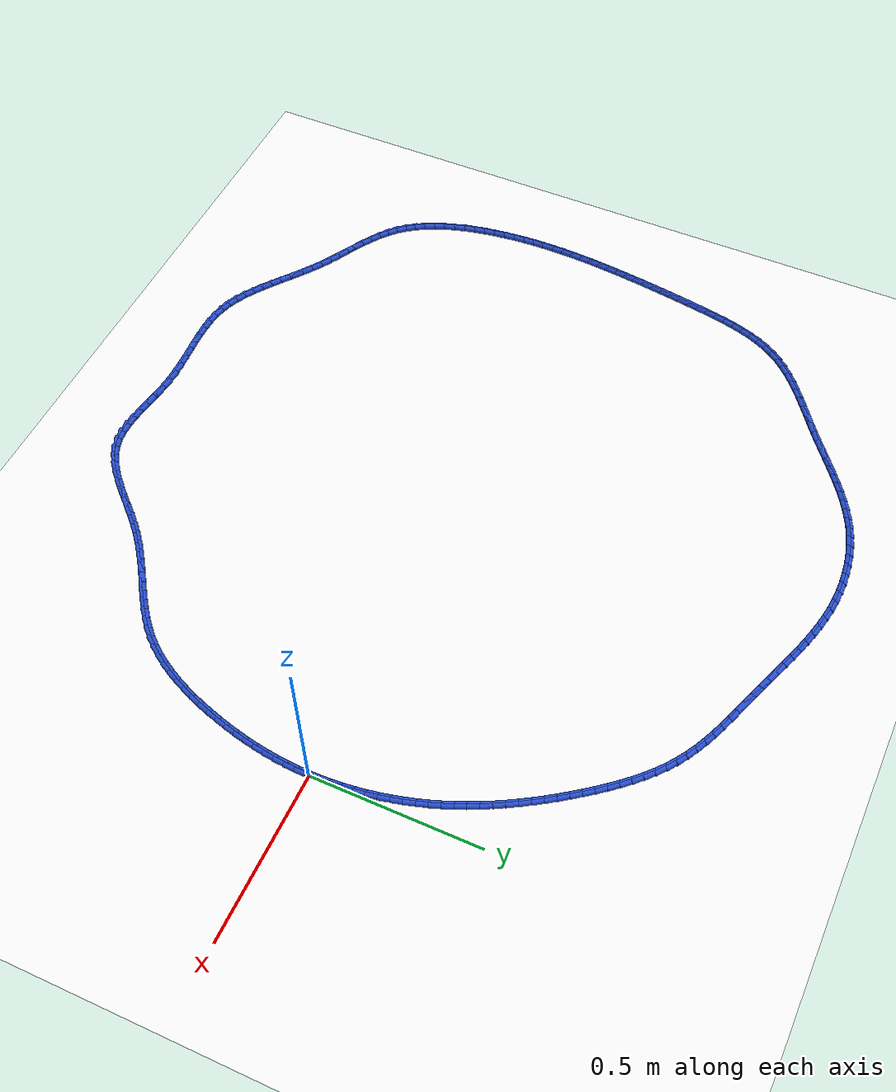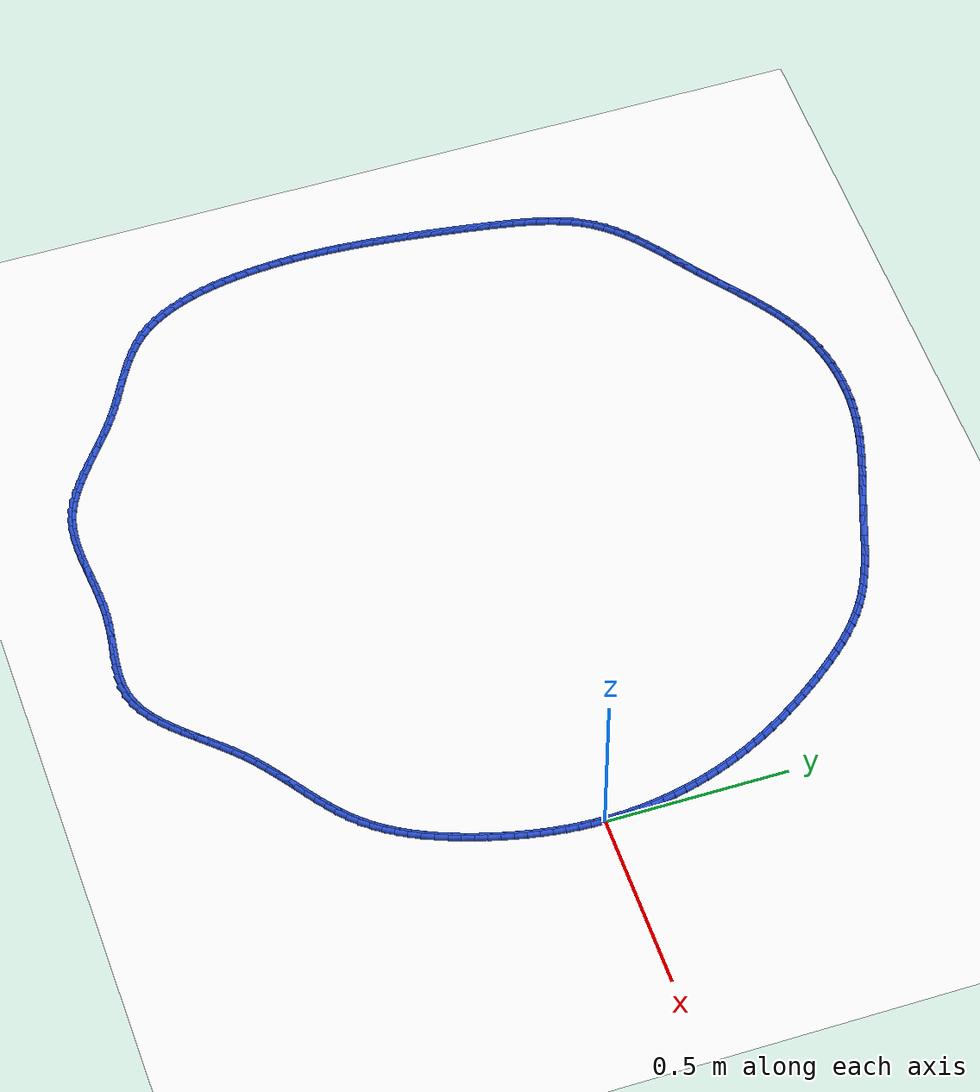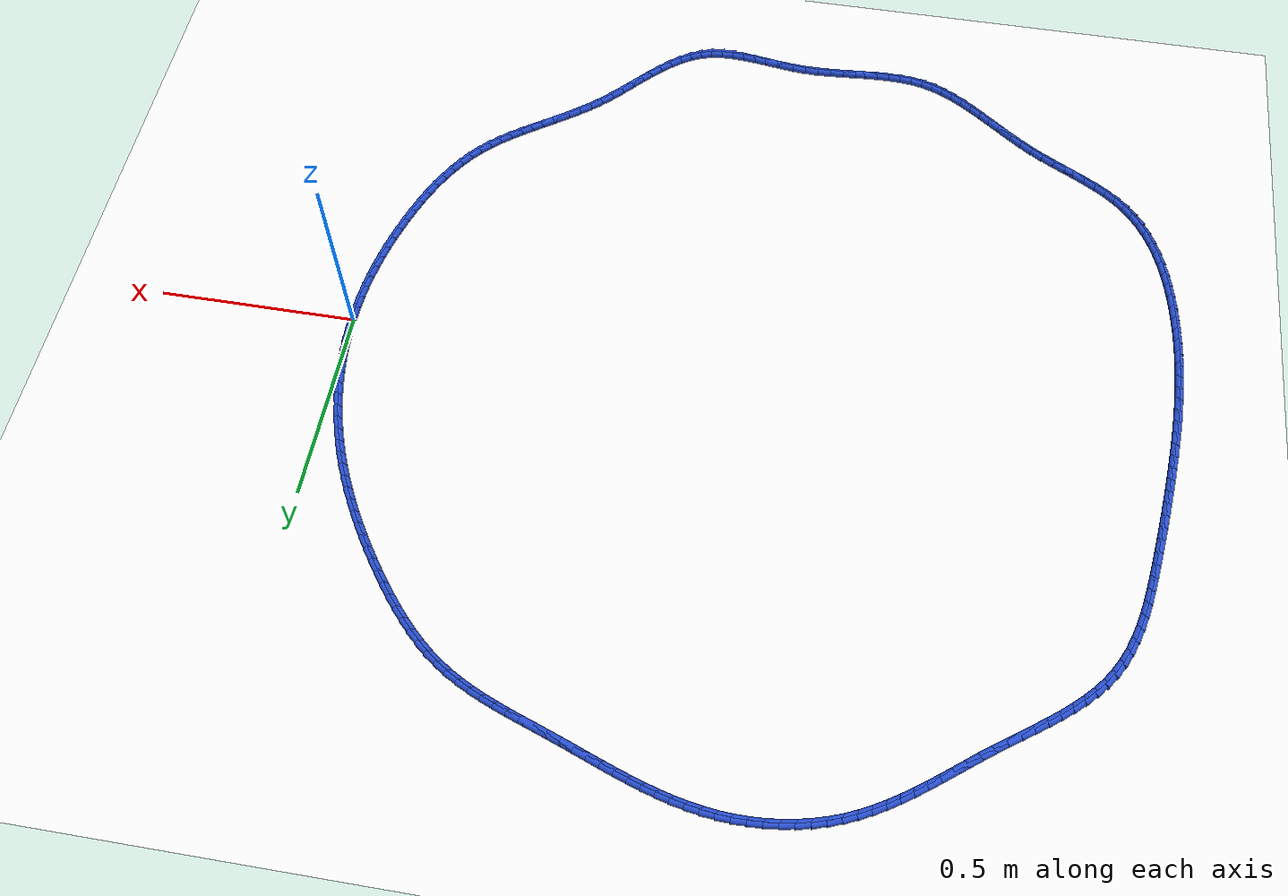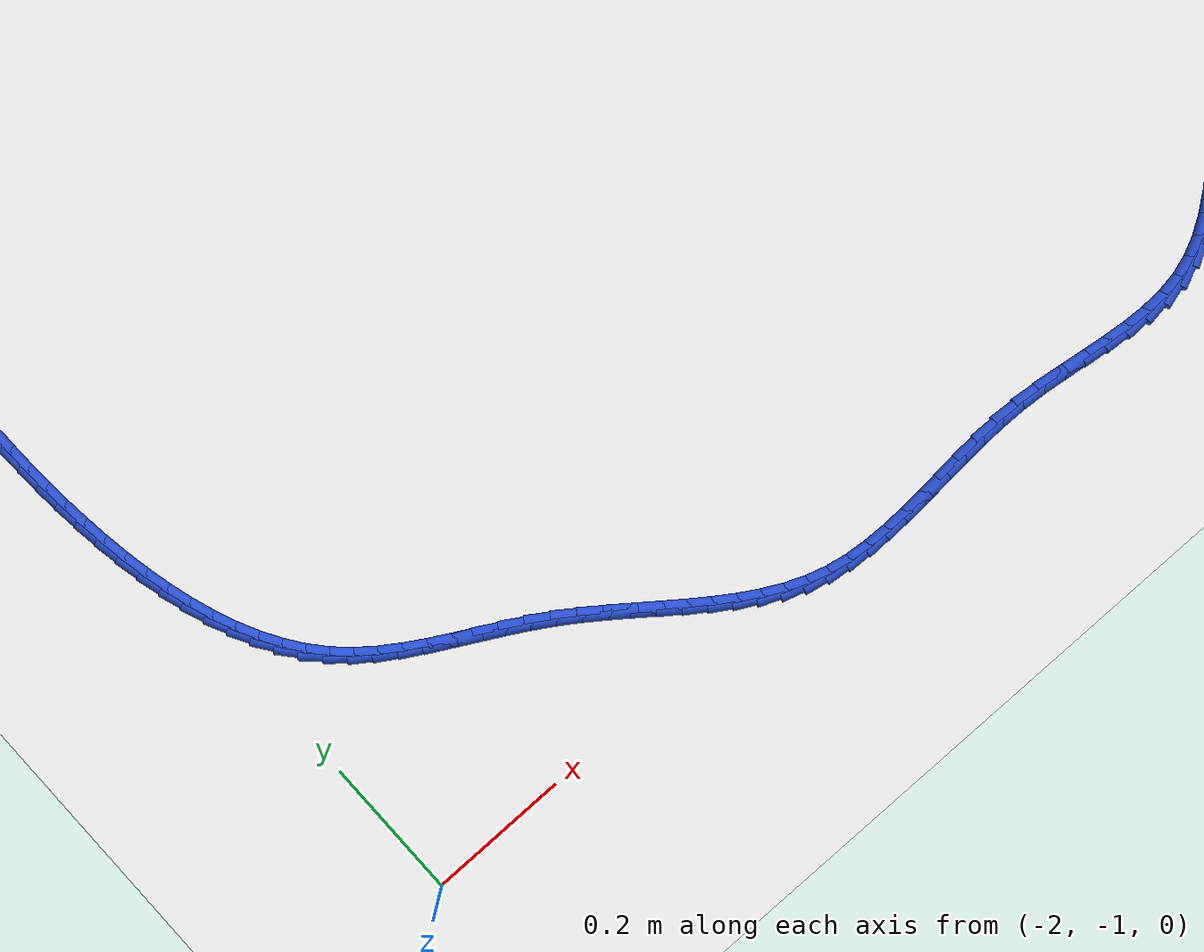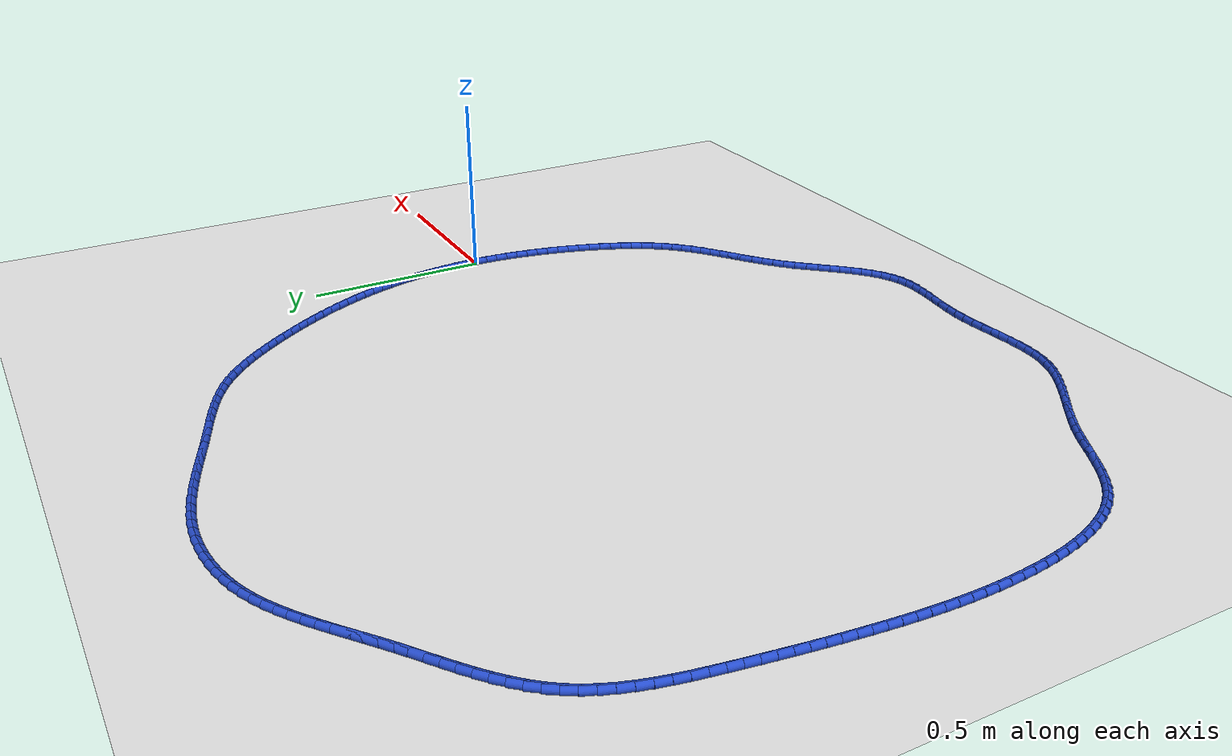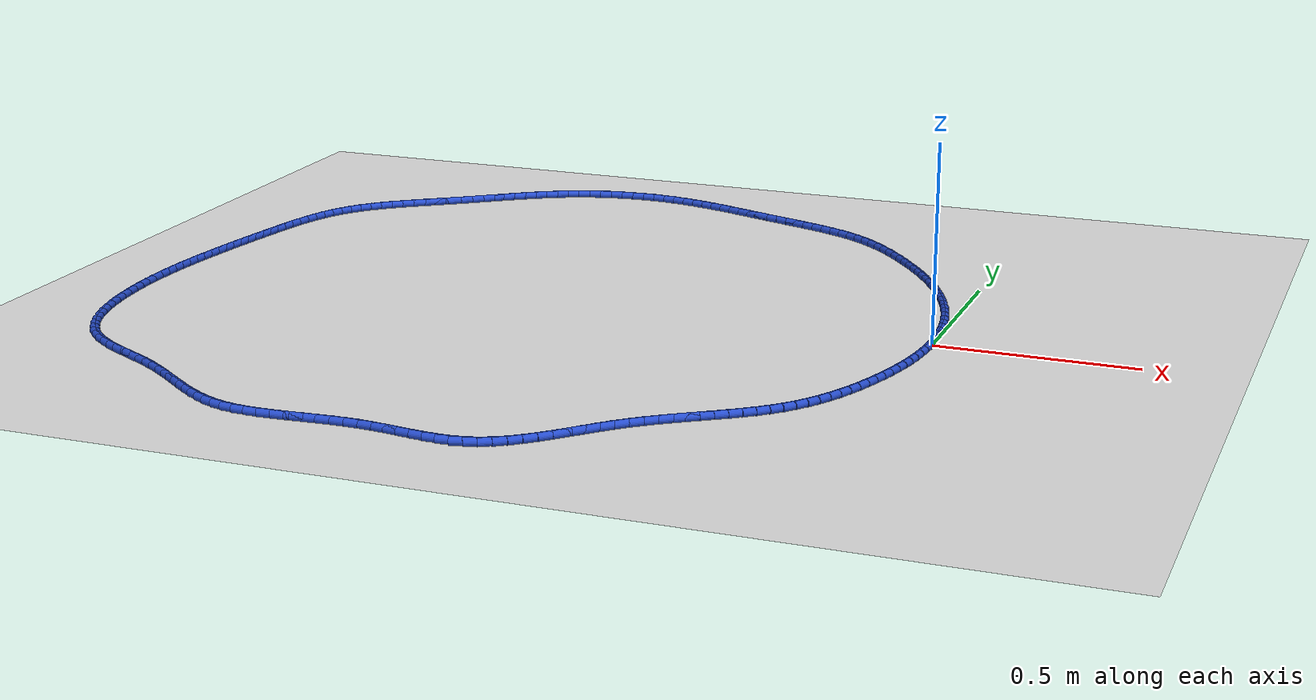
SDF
<sdf version="1.6">
 <world name="default">
  <light name="sun" type="directional">
   <pose>0 0 10 0 -0 0</pose>
   <diffuse>0.8 0.8 0.8 1</diffuse>
   <specular>0.2 0.2 0.2 1</specular>
   <attenuation>
    <range>1000</range>
    <constant>0.9</constant>
    <linear>0.01</linear>
    <quadratic>0.001</quadratic>
   </attenuation>
   <direction>-0.5 0.1 -0.9</direction>
  </light>
  <model name="ground_plane">
   <static>1</static>
   <link name="link">
    <collision name="collision">
     <geometry><plane><normal>0 0 1</normal><size>100 100</size></plane></geometry>
     <surface><friction><ode><mu>100</mu><mu2>50</mu2></ode></friction></surface>
    </collision>
    <visual name="visual">
     <cast_shadows>0</cast_shadows>
     <geometry><plane><normal>0 0 1</normal><size>100 100</size></plane></geometry>
     <material>
      <script><uri>file://media/materials/scripts/gazebo.material</uri><name>Gazebo/WhiteGlow</name></script>
     </material>
    </visual>
   </link>
  </model>
  <gravity>0 0 -9.8</gravity>
  <magnetic_field>6e-06 2.3e-05 -4.2e-05</magnetic_field>
  <atmosphere type="adiabatic"/>
  <physics name="default_physics" default="0" type="ode">
   <max_step_size>0.001</max_step_size>
   <real_time_factor>1</real_time_factor>
   <real_time_update_rate>1000</real_time_update_rate>
  </physics>
  <scene><ambient>0.4 0.4 0.4 1</ambient><background>0.7 0.7 0.7 1</background><shadows>1</shadows></scene>
  <spherical_coordinates>
   <surface_model>EARTH_WGS84</surface_model>
   <latitude_deg>0</latitude_deg>
   <longitude_deg>0</longitude_deg>
   <elevation>0</elevation>
   <heading_deg>0</heading_deg>
  </spherical_coordinates>
  <model name="line">
   <link name="link_0">
    <pose>3.469446951953614e-18 -4.85722573273506e-17 0.01 0 1.57 -1.557743112268379</pose>
    <collision name="collision">
     <geometry><cylinder><radius>0.01</radius><length>0.08</length></cylinder></geometry>
    </collision>
    <visual name="visual">
     <material>
      <script><name>Gazebo/Blue</name><uri>file://media/materials/scripts/gazebo.material</uri></script>
     </material>
     <geometry><cylinder><radius>0.01</radius><length>0.08</length></cylinder></geometry>
    </visual>
   </link>
   <link name="link_1">
    <pose>-0.0004305091601614278 0.03297921044958965 0.01 0 1.57 -1.5230656228391661</pose>
    <collision name="collision">
     <geometry><cylinder><radius>0.01</radius><length>0.08</length></cylinder></geometry>
    </collision>
    <visual name="visual">
     <material>
      <script><name>Gazebo/Blue</name><uri>file://media/materials/scripts/gazebo.material</uri></script>
     </material>
     <geometry><cylinder><radius>0.01</radius><length>0.08</length></cylinder></geometry>
    </visual>
   </link>
   <link name="link_2">
    <pose>-0.0020077572388519137 0.06599883918657329 0.01 0 1.57 -1.4888375087633177</pose>
    <collision name="collision">
     <geometry><cylinder><radius>0.01</radius><length>0.08</length></cylinder></geometry>
    </collision>
    <visual name="visual">
     <material>
      <script><name>Gazebo/Blue</name><uri>file://media/materials/scripts/gazebo.material</uri></script>
     </material>
     <geometry><cylinder><radius>0.01</radius><length>0.08</length></cylinder></geometry>
    </visual>
   </link>
   <link name="link_3">
    <pose>-0.004718978539279356 0.09900502444685318 0.01 0 1.57 -1.4549674211429733</pose>
    <collision name="collision">
     <geometry><cylinder><radius>0.01</radius><length>0.08</length></cylinder></geometry>
    </collision>
    <visual name="visual">
     <material>
      <script><name>Gazebo/Blue</name><uri>file://media/materials/scripts/gazebo.material</uri></script>
     </material>
     <geometry><cylinder><radius>0.01</radius><length>0.08</length></cylinder></geometry>
    </visual>
   </link>
   <link name="link_4">
    <pose>-0.008551407364651669 0.1319439044663319 0.01 0 1.57 -1.4213636399968868</pose>
    <collision name="collision">
     <geometry><cylinder><radius>0.01</radius><length>0.08</length></cylinder></geometry>
    </collision>
    <visual name="visual">
     <material>
      <script><name>Gazebo/Blue</name><uri>file://media/materials/scripts/gazebo.material</uri></script>
     </material>
     <geometry><cylinder><radius>0.01</radius><length>0.08</length></cylinder></geometry>
    </visual>
   </link>
   <link name="link_5">
    <pose>-0.01349227801817674 0.16476161748091164 0.01 0 1.57 -1.3879341648001446</pose>
    <collision name="collision">
     <geometry><cylinder><radius>0.01</radius><length>0.08</length></cylinder></geometry>
    </collision>
    <visual name="visual">
     <material>
      <script><name>Gazebo/Blue</name><uri>file://media/materials/scripts/gazebo.material</uri></script>
     </material>
     <geometry><cylinder><radius>0.01</radius><length>0.08</length></cylinder></geometry>
    </visual>
   </link>
   <link name="link_6">
    <pose>-0.019528824803062478 0.19740430172649504 0.01 0 1.57 -1.3545867331646058</pose>
    <collision name="collision">
     <geometry><cylinder><radius>0.01</radius><length>0.08</length></cylinder></geometry>
    </collision>
    <visual name="visual">
     <material>
      <script><name>Gazebo/Blue</name><uri>file://media/materials/scripts/gazebo.material</uri></script>
     </material>
     <geometry><cylinder><radius>0.01</radius><length>0.08</length></cylinder></geometry>
    </visual>
   </link>
   <link name="link_7">
    <pose>-0.026648282022516796 0.22981809543898435 0.01 0 1.57 -1.3212287914505034</pose>
    <collision name="collision">
     <geometry><cylinder><radius>0.01</radius><length>0.08</length></cylinder></geometry>
    </collision>
    <visual name="visual">
     <material>
      <script><name>Gazebo/Blue</name><uri>file://media/materials/scripts/gazebo.material</uri></script>
     </material>
     <geometry><cylinder><radius>0.01</radius><length>0.08</length></cylinder></geometry>
    </visual>
   </link>
   <link name="link_8">
    <pose>-0.034837883979747575 0.26194913685428206 0.01 0 1.57 -1.2877674400181622</pose>
    <collision name="collision">
     <geometry><cylinder><radius>0.01</radius><length>0.08</length></cylinder></geometry>
    </collision>
    <visual name="visual">
     <material>
      <script><name>Gazebo/Blue</name><uri>file://media/materials/scripts/gazebo.material</uri></script>
     </material>
     <geometry><cylinder><radius>0.01</radius><length>0.08</length></cylinder></geometry>
    </visual>
   </link>
   <link name="link_9">
    <pose>-0.04408486497796271 0.2937435642082904 0.01 0 1.57 -1.2541393315151732</pose>
    <collision name="collision">
     <geometry><cylinder><radius>0.01</radius><length>0.08</length></cylinder></geometry>
    </collision>
    <visual name="visual">
     <material>
      <script><name>Gazebo/Blue</name><uri>file://media/materials/scripts/gazebo.material</uri></script>
     </material>
     <geometry><cylinder><radius>0.01</radius><length>0.08</length></cylinder></geometry>
    </visual>
   </link>
   <link name="link_10">
    <pose>-0.05437586806152327 0.3251488905540832 0.01 0 1.57 -1.2209216455504501</pose>
    <collision name="collision">
     <geometry><cylinder><radius>0.01</radius><length>0.08</length></cylinder></geometry>
    </collision>
    <visual name="visual">
     <material>
      <script><name>Gazebo/Blue</name><uri>file://media/materials/scripts/gazebo.material</uri></script>
     </material>
     <geometry><cylinder><radius>0.01</radius><length>0.08</length></cylinder></geometry>
    </visual>
   </link>
   <link name="link_11">
    <pose>-0.06568486695827308 0.35614208811305703 0.01 0 1.57 -1.1887616874989992</pose>
    <collision name="collision">
     <geometry><cylinder><radius>0.01</radius><length>0.08</length></cylinder></geometry>
    </collision>
    <visual name="visual">
     <material>
      <script><name>Gazebo/Blue</name><uri>file://media/materials/scripts/gazebo.material</uri></script>
     </material>
     <geometry><cylinder><radius>0.01</radius><length>0.08</length></cylinder></geometry>
    </visual>
   </link>
   <link name="link_12">
    <pose>-0.07797366198444956 0.386728435178298 0.01 0 1.57 -1.157730970514075</pose>
    <collision name="collision">
     <geometry><cylinder><radius>0.01</radius><length>0.08</length></cylinder></geometry>
    </collision>
    <visual name="visual">
     <material>
      <script><name>Gazebo/Blue</name><uri>file://media/materials/scripts/gazebo.material</uri></script>
     </material>
     <geometry><cylinder><radius>0.01</radius><length>0.08</length></cylinder></geometry>
    </visual>
   </link>
   <link name="link_13">
    <pose>-0.09120356142799732 0.4169143541254702 0.01 0 1.57 -1.1278642688266343</pose>
    <collision name="collision">
     <geometry><cylinder><radius>0.01</radius><length>0.08</length></cylinder></geometry>
    </collision>
    <visual name="visual">
     <material>
      <script><name>Gazebo/Blue</name><uri>file://media/materials/scripts/gazebo.material</uri></script>
     </material>
     <geometry><cylinder><radius>0.01</radius><length>0.08</length></cylinder></geometry>
    </visual>
   </link>
   <link name="link_14">
    <pose>-0.10533587357686097 0.4467062673302369 0.01 0 1.57 -1.0991854840167534</pose>
    <collision name="collision">
     <geometry><cylinder><radius>0.01</radius><length>0.08</length></cylinder></geometry>
    </collision>
    <visual name="visual">
     <material>
      <script><name>Gazebo/Blue</name><uri>file://media/materials/scripts/gazebo.material</uri></script>
     </material>
     <geometry><cylinder><radius>0.01</radius><length>0.08</length></cylinder></geometry>
    </visual>
   </link>
   <link name="link_15">
    <pose>-0.12033190671898503 0.47611059716826165 0.01 0 1.57 -1.0717087342456912</pose>
    <collision name="collision">
     <geometry><cylinder><radius>0.01</radius><length>0.08</length></cylinder></geometry>
    </collision>
    <visual name="visual">
     <material>
      <script><name>Gazebo/Blue</name><uri>file://media/materials/scripts/gazebo.material</uri></script>
     </material>
     <geometry><cylinder><radius>0.01</radius><length>0.08</length></cylinder></geometry>
    </visual>
   </link>
   <link name="link_16">
    <pose>-0.1361529691423143 0.5051337660152084 0.01 0 1.57 -1.0454395284814884</pose>
    <collision name="collision">
     <geometry><cylinder><radius>0.01</radius><length>0.08</length></cylinder></geometry>
    </collision>
    <visual name="visual">
     <material>
      <script><name>Gazebo/Blue</name><uri>file://media/materials/scripts/gazebo.material</uri></script>
     </material>
     <geometry><cylinder><radius>0.01</radius><length>0.08</length></cylinder></geometry>
    </visual>
   </link>
   <link name="link_17">
    <pose>-0.1527603691347933 0.5337821962467407 0.01 0 1.57 -1.020375970094882</pose>
    <collision name="collision">
     <geometry><cylinder><radius>0.01</radius><length>0.08</length></cylinder></geometry>
    </collision>
    <visual name="visual">
     <material>
      <script><name>Gazebo/Blue</name><uri>file://media/materials/scripts/gazebo.material</uri></script>
     </material>
     <geometry><cylinder><radius>0.01</radius><length>0.08</length></cylinder></geometry>
    </visual>
   </link>
   <link name="link_18">
    <pose>-0.1701154149843666 0.5620623102385222 0.01 0 1.57 -0.9965099449236364</pose>
    <collision name="collision">
     <geometry><cylinder><radius>0.01</radius><length>0.08</length></cylinder></geometry>
    </collision>
    <visual name="visual">
     <material>
      <script><name>Gazebo/Blue</name><uri>file://media/materials/scripts/gazebo.material</uri></script>
     </material>
     <geometry><cylinder><radius>0.01</radius><length>0.08</length></cylinder></geometry>
    </visual>
   </link>
   <link name="link_19">
    <pose>-0.1881794149789789 0.5899805303662163 0.01 0 1.57 -0.9738282597687575</pose>
    <collision name="collision">
     <geometry><cylinder><radius>0.01</radius><length>0.08</length></cylinder></geometry>
    </collision>
    <visual name="visual">
     <material>
      <script><name>Gazebo/Blue</name><uri>file://media/materials/scripts/gazebo.material</uri></script>
     </material>
     <geometry><cylinder><radius>0.01</radius><length>0.08</length></cylinder></geometry>
    </visual>
   </link>
   <link name="link_20">
    <pose>-0.20691367740657482 0.617543279005487 0.01 0 1.57 -0.9523137074415136</pose>
    <collision name="collision">
     <geometry><cylinder><radius>0.01</radius><length>0.08</length></cylinder></geometry>
    </collision>
    <visual name="visual">
     <material>
      <script><name>Gazebo/Blue</name><uri>file://media/materials/scripts/gazebo.material</uri></script>
     </material>
     <geometry><cylinder><radius>0.01</radius><length>0.08</length></cylinder></geometry>
    </visual>
   </link>
   <link name="link_21">
    <pose>-0.22627951055509893 0.6447569785319979 0.01 0 1.57 -0.9319460433943224</pose>
    <collision name="collision">
     <geometry><cylinder><radius>0.01</radius><length>0.08</length></cylinder></geometry>
    </collision>
    <visual name="visual">
     <material>
      <script><name>Gazebo/Blue</name><uri>file://media/materials/scripts/gazebo.material</uri></script>
     </material>
     <geometry><cylinder><radius>0.01</radius><length>0.08</length></cylinder></geometry>
    </visual>
   </link>
   <link name="link_22">
    <pose>-0.24623822271249574 0.6716280513214121 0.01 0 1.57 -0.9121768304989757</pose>
    <collision name="collision">
     <geometry><cylinder><radius>0.01</radius><length>0.08</length></cylinder></geometry>
    </collision>
    <visual name="visual">
     <material>
      <script><name>Gazebo/Blue</name><uri>file://media/materials/scripts/gazebo.material</uri></script>
     </material>
     <geometry><cylinder><radius>0.01</radius><length>0.08</length></cylinder></geometry>
    </visual>
   </link>
   <link name="link_23">
    <pose>-0.26676074513045 0.6981465272667619 0.01 0 1.57 -0.8890715615643078</pose>
    <collision name="collision">
     <geometry><cylinder><radius>0.01</radius><length>0.08</length></cylinder></geometry>
    </collision>
    <visual name="visual">
     <material>
      <script><name>Gazebo/Blue</name><uri>file://media/materials/scripts/gazebo.material</uri></script>
     </material>
     <geometry><cylinder><radius>0.01</radius><length>0.08</length></cylinder></geometry>
    </visual>
   </link>
   <link name="link_24">
    <pose>-0.28788883141735166 0.7241817921140499 0.01 0 1.57 -0.8607309890439699</pose>
    <collision name="collision">
     <geometry><cylinder><radius>0.01</radius><length>0.08</length></cylinder></geometry>
    </collision>
    <visual name="visual">
     <material>
      <script><name>Gazebo/Blue</name><uri>file://media/materials/scripts/gazebo.material</uri></script>
     </material>
     <geometry><cylinder><radius>0.01</radius><length>0.08</length></cylinder></geometry>
    </visual>
   </link>
   <link name="link_25">
    <pose>-0.30969586198591387 0.749549356124075 0.01 0 1.57 -0.8269172972775372</pose>
    <collision name="collision">
     <geometry><cylinder><radius>0.01</radius><length>0.08</length></cylinder></geometry>
    </collision>
    <visual name="visual">
     <material>
      <script><name>Gazebo/Blue</name><uri>file://media/materials/scripts/gazebo.material</uri></script>
     </material>
     <geometry><cylinder><radius>0.01</radius><length>0.08</length></cylinder></geometry>
    </visual>
   </link>
   <link name="link_26">
    <pose>-0.33225536396307703 0.774064479633551 0.01 0 1.57 -0.7873707609153084</pose>
    <collision name="collision">
     <geometry><cylinder><radius>0.01</radius><length>0.08</length></cylinder></geometry>
    </collision>
    <visual name="visual">
     <material>
      <script><name>Gazebo/Blue</name><uri>file://media/materials/scripts/gazebo.material</uri></script>
     </material>
     <geometry><cylinder><radius>0.01</radius><length>0.08</length></cylinder></geometry>
    </visual>
   </link>
   <link name="link_27">
    <pose>-0.3556408644757811 0.7975424229791911 0.01 0 1.57 -0.741829771908615</pose>
    <collision name="collision">
     <geometry><cylinder><radius>0.01</radius><length>0.08</length></cylinder></geometry>
    </collision>
    <visual name="visual">
     <material>
      <script><name>Gazebo/Blue</name><uri>file://media/materials/scripts/gazebo.material</uri></script>
     </material>
     <geometry><cylinder><radius>0.01</radius><length>0.08</length></cylinder></geometry>
    </visual>
   </link>
   <link name="link_28">
    <pose>-0.37992589065096627 0.8197984464977087 0.01 0 1.57 -0.6900696915647543</pose>
    <collision name="collision">
     <geometry><cylinder><radius>0.01</radius><length>0.08</length></cylinder></geometry>
    </collision>
    <visual name="visual">
     <material>
      <script><name>Gazebo/Blue</name><uri>file://media/materials/scripts/gazebo.material</uri></script>
     </material>
     <geometry><cylinder><radius>0.01</radius><length>0.08</length></cylinder></geometry>
    </visual>
   </link>
   <link name="link_29">
    <pose>-0.4051839696155728 0.840647810525817 0.01 0 1.57 -0.6319543618539908</pose>
    <collision name="collision">
     <geometry><cylinder><radius>0.01</radius><length>0.08</length></cylinder></geometry>
    </collision>
    <visual name="visual">
     <material>
      <script><name>Gazebo/Blue</name><uri>file://media/materials/scripts/gazebo.material</uri></script>
     </material>
     <geometry><cylinder><radius>0.01</radius><length>0.08</length></cylinder></geometry>
    </visual>
   </link>
   <link name="link_30">
    <pose>-0.43148862849654096 0.8599057754002297 0.01 0 1.57 -0.5688159105620555</pose>
    <collision name="collision">
     <geometry><cylinder><radius>0.01</radius><length>0.08</length></cylinder></geometry>
    </collision>
    <visual name="visual">
     <material>
      <script><name>Gazebo/Blue</name><uri>file://media/materials/scripts/gazebo.material</uri></script>
     </material>
     <geometry><cylinder><radius>0.01</radius><length>0.08</length></cylinder></geometry>
    </visual>
   </link>
   <link name="link_31">
    <pose>-0.458893856802592 0.8774259174753867 0.01 0 1.57 -0.5100819666789304</pose>
    <collision name="collision">
     <geometry><cylinder><radius>0.01</radius><length>0.08</length></cylinder></geometry>
    </collision>
    <visual name="visual">
     <material>
      <script><name>Gazebo/Blue</name><uri>file://media/materials/scripts/gazebo.material</uri></script>
     </material>
     <geometry><cylinder><radius>0.01</radius><length>0.08</length></cylinder></geometry>
    </visual>
   </link>
   <link name="link_32">
    <pose>-0.4873178260382334 0.893328171317812 0.01 0 1.57 -0.4599771303934672</pose>
    <collision name="collision">
     <geometry><cylinder><radius>0.01</radius><length>0.08</length></cylinder></geometry>
    </collision>
    <visual name="visual">
     <material>
      <script><name>Gazebo/Blue</name><uri>file://media/materials/scripts/gazebo.material</uri></script>
     </material>
     <geometry><cylinder><radius>0.01</radius><length>0.08</length></cylinder></geometry>
    </visual>
   </link>
   <link name="link_33">
    <pose>-0.5166210351235947 0.9078455755449256 0.01 0 1.57 -0.41860443215029297</pose>
    <collision name="collision">
     <geometry><cylinder><radius>0.01</radius><length>0.08</length></cylinder></geometry>
    </collision>
    <visual name="visual">
     <material>
      <script><name>Gazebo/Blue</name><uri>file://media/materials/scripts/gazebo.material</uri></script>
     </material>
     <geometry><cylinder><radius>0.01</radius><length>0.08</length></cylinder></geometry>
    </visual>
   </link>
   <link name="link_34">
    <pose>-0.5466637729087572 0.921211580751061 0.01 0 1.57 -0.3858691867354731</pose>
    <collision name="collision">
     <geometry><cylinder><radius>0.01</radius><length>0.08</length></cylinder></geometry>
    </collision>
    <visual name="visual">
     <material>
      <script><name>Gazebo/Blue</name><uri>file://media/materials/scripts/gazebo.material</uri></script>
     </material>
     <geometry><cylinder><radius>0.01</radius><length>0.08</length></cylinder></geometry>
    </visual>
   </link>
   <link name="link_35">
    <pose>-0.5773063282438031 0.9336596375305528 0.01 0 1.57 -0.3615881659650599</pose>
    <collision name="collision">
     <geometry><cylinder><radius>0.01</radius><length>0.08</length></cylinder></geometry>
    </collision>
    <visual name="visual">
     <material>
      <script><name>Gazebo/Blue</name><uri>file://media/materials/scripts/gazebo.material</uri></script>
     </material>
     <geometry><cylinder><radius>0.01</radius><length>0.08</length></cylinder></geometry>
    </visual>
   </link>
   <link name="link_36">
    <pose>-0.608408989978814 0.9454231964777349 0.01 0 1.57 -0.3455615304689277</pose>
    <collision name="collision">
     <geometry><cylinder><radius>0.01</radius><length>0.08</length></cylinder></geometry>
    </collision>
    <visual name="visual">
     <material>
      <script><name>Gazebo/Blue</name><uri>file://media/materials/scripts/gazebo.material</uri></script>
     </material>
     <geometry><cylinder><radius>0.01</radius><length>0.08</length></cylinder></geometry>
    </visual>
   </link>
   <link name="link_37">
    <pose>-0.6398320469638716 0.9567357081869414 0.01 0 1.57 -0.33762180595355923</pose>
    <collision name="collision">
     <geometry><cylinder><radius>0.01</radius><length>0.08</length></cylinder></geometry>
    </collision>
    <visual name="visual">
     <material>
      <script><name>Gazebo/Blue</name><uri>file://media/materials/scripts/gazebo.material</uri></script>
     </material>
     <geometry><cylinder><radius>0.01</radius><length>0.08</length></cylinder></geometry>
    </visual>
   </link>
   <link name="link_38">
    <pose>-0.6714357880490576 0.967830623252506 0.01 0 1.57 -0.3376631574070777</pose>
    <collision name="collision">
     <geometry><cylinder><radius>0.01</radius><length>0.08</length></cylinder></geometry>
    </collision>
    <visual name="visual">
     <material>
      <script><name>Gazebo/Blue</name><uri>file://media/materials/scripts/gazebo.material</uri></script>
     </material>
     <geometry><cylinder><radius>0.01</radius><length>0.08</length></cylinder></geometry>
    </visual>
   </link>
   <link name="link_39">
    <pose>-0.7030805020844538 0.9789413922687629 0.01 0 1.57 -0.34504169216447694</pose>
    <collision name="collision">
     <geometry><cylinder><radius>0.01</radius><length>0.08</length></cylinder></geometry>
    </collision>
    <visual name="visual">
     <material>
      <script><name>Gazebo/Blue</name><uri>file://media/materials/scripts/gazebo.material</uri></script>
     </material>
     <geometry><cylinder><radius>0.01</radius><length>0.08</length></cylinder></geometry>
    </visual>
   </link>
   <link name="link_40">
    <pose>-0.734634821170663 0.9902826336113713 0.01 0 1.57 -0.35214061430597116</pose>
    <collision name="collision">
     <geometry><cylinder><radius>0.01</radius><length>0.08</length></cylinder></geometry>
    </collision>
    <visual name="visual">
     <material>
      <script><name>Gazebo/Blue</name><uri>file://media/materials/scripts/gazebo.material</uri></script>
     </material>
     <geometry><cylinder><radius>0.01</radius><length>0.08</length></cylinder></geometry>
    </visual>
   </link>
   <link name="link_41">
    <pose>-0.7660713875571105 1.0018341960224764 0.01 0 1.57 -0.353774809815372</pose>
    <collision name="collision">
     <geometry><cylinder><radius>0.01</radius><length>0.08</length></cylinder></geometry>
    </collision>
    <visual name="visual">
     <material>
      <script><name>Gazebo/Blue</name><uri>file://media/materials/scripts/gazebo.material</uri></script>
     </material>
     <geometry><cylinder><radius>0.01</radius><length>0.08</length></cylinder></geometry>
    </visual>
   </link>
   <link name="link_42">
    <pose>-0.7974334378866961 1.013416583987232 0.01 0 1.57 -0.34981889681767375</pose>
    <collision name="collision">
     <geometry><cylinder><radius>0.01</radius><length>0.08</length></cylinder></geometry>
    </collision>
    <visual name="visual">
     <material>
      <script><name>Gazebo/Blue</name><uri>file://media/materials/scripts/gazebo.material</uri></script>
     </material>
     <geometry><cylinder><radius>0.01</radius><length>0.08</length></cylinder></geometry>
    </visual>
   </link>
   <link name="link_43">
    <pose>-0.8287655526533967 1.0248472686769419 0.01 0 1.57 -0.3402253253928257</pose>
    <collision name="collision">
     <geometry><cylinder><radius>0.01</radius><length>0.08</length></cylinder></geometry>
    </collision>
    <visual name="visual">
     <material>
      <script><name>Gazebo/Blue</name><uri>file://media/materials/scripts/gazebo.material</uri></script>
     </material>
     <geometry><cylinder><radius>0.01</radius><length>0.08</length></cylinder></geometry>
    </visual>
   </link>
   <link name="link_44">
    <pose>-0.8601123123511887 1.03594372126291 0.01 0 1.57 -0.3249289532018291</pose>
    <collision name="collision">
     <geometry><cylinder><radius>0.01</radius><length>0.08</length></cylinder></geometry>
    </collision>
    <visual name="visual">
     <material>
      <script><name>Gazebo/Blue</name><uri>file://media/materials/scripts/gazebo.material</uri></script>
     </material>
     <geometry><cylinder><radius>0.01</radius><length>0.08</length></cylinder></geometry>
    </visual>
   </link>
   <link name="link_45">
    <pose>-0.8915182974740493 1.0465234129164405 0.01 0 1.57 -0.3038558131596806</pose>
    <collision name="collision">
     <geometry><cylinder><radius>0.01</radius><length>0.08</length></cylinder></geometry>
    </collision>
    <visual name="visual">
     <material>
      <script><name>Gazebo/Blue</name><uri>file://media/materials/scripts/gazebo.material</uri></script>
     </material>
     <geometry><cylinder><radius>0.01</radius><length>0.08</length></cylinder></geometry>
    </visual>
   </link>
   <link name="link_46">
    <pose>-0.9230280885159549 1.0564038148088366 0.01 0 1.57 -0.27693794954460715</pose>
    <collision name="collision">
     <geometry><cylinder><radius>0.01</radius><length>0.08</length></cylinder></geometry>
    </collision>
    <visual name="visual">
     <material>
      <script><name>Gazebo/Blue</name><uri>file://media/materials/scripts/gazebo.material</uri></script>
     </material>
     <geometry><cylinder><radius>0.01</radius><length>0.08</length></cylinder></geometry>
    </visual>
   </link>
   <link name="link_47">
    <pose>-0.9546862659708824 1.065402398111403 0.01 0 1.57 -0.24413484902911714</pose>
    <collision name="collision">
     <geometry><cylinder><radius>0.01</radius><length>0.08</length></cylinder></geometry>
    </collision>
    <visual name="visual">
     <material>
      <script><name>Gazebo/Blue</name><uri>file://media/materials/scripts/gazebo.material</uri></script>
     </material>
     <geometry><cylinder><radius>0.01</radius><length>0.08</length></cylinder></geometry>
    </visual>
   </link>
   <link name="link_48">
    <pose>-0.9865374103328084 1.0733366339954429 0.01 0 1.57 -0.20546155986984965</pose>
    <collision name="collision">
     <geometry><cylinder><radius>0.01</radius><length>0.08</length></cylinder></geometry>
    </collision>
    <visual name="visual">
     <material>
      <script><name>Gazebo/Blue</name><uri>file://media/materials/scripts/gazebo.material</uri></script>
     </material>
     <geometry><cylinder><radius>0.01</radius><length>0.08</length></cylinder></geometry>
    </visual>
   </link>
   <link name="link_49">
    <pose>-1.01862610209571 1.0800239936322606 0.01 0 1.57 -0.1610225706911706</pose>
    <collision name="collision">
     <geometry><cylinder><radius>0.01</radius><length>0.08</length></cylinder></geometry>
    </collision>
    <visual name="visual">
     <material>
      <script><name>Gazebo/Blue</name><uri>file://media/materials/scripts/gazebo.material</uri></script>
     </material>
     <geometry><cylinder><radius>0.01</radius><length>0.08</length></cylinder></geometry>
    </visual>
   </link>
   <link name="link_50">
    <pose>-1.050996921753564 1.0852819481931602 0.01 0 1.57 -0.11104879064355587</pose>
    <collision name="collision">
     <geometry><cylinder><radius>0.01</radius><length>0.08</length></cylinder></geometry>
    </collision>
    <visual name="visual">
     <material>
      <script><name>Gazebo/Blue</name><uri>file://media/materials/scripts/gazebo.material</uri></script>
     </material>
     <geometry><cylinder><radius>0.01</radius><length>0.08</length></cylinder></geometry>
    </visual>
   </link>
   <link name="link_51">
    <pose>-1.0836944498003471 1.0889279688494455 0.01 0 1.57 -0.056286742615134736</pose>
    <collision name="collision">
     <geometry><cylinder><radius>0.01</radius><length>0.08</length></cylinder></geometry>
    </collision>
    <visual name="visual">
     <material>
      <script><name>Gazebo/Blue</name><uri>file://media/materials/scripts/gazebo.material</uri></script>
     </material>
     <geometry><cylinder><radius>0.01</radius><length>0.08</length></cylinder></geometry>
    </visual>
   </link>
   <link name="link_52">
    <pose>-1.1167486339495993 1.09079044852165 0.01 0 1.57 -0.00036332663223348683</pose>
    <collision name="collision">
     <geometry><cylinder><radius>0.01</radius><length>0.08</length></cylinder></geometry>
    </collision>
    <visual name="visual">
     <material>
      <script><name>Gazebo/Blue</name><uri>file://media/materials/scripts/gazebo.material</uri></script>
     </material>
     <geometry><cylinder><radius>0.01</radius><length>0.08</length></cylinder></geometry>
    </visual>
   </link>
   <link name="link_53">
    <pose>-1.1500490563753827 1.0908025474525143 0.01 0 1.57 0.05530546310357478</pose>
    <collision name="collision">
     <geometry><cylinder><radius>0.01</radius><length>0.08</length></cylinder></geometry>
    </collision>
    <visual name="visual">
     <material>
      <script><name>Gazebo/Blue</name><uri>file://media/materials/scripts/gazebo.material</uri></script>
     </material>
     <geometry><cylinder><radius>0.01</radius><length>0.08</length></cylinder></geometry>
    </visual>
   </link>
   <link name="link_54">
    <pose>-1.1834071156878332 1.0889557812522248 0.01 0 1.57 0.111301697875346</pose>
    <collision name="collision">
     <geometry><cylinder><radius>0.01</radius><length>0.08</length></cylinder></geometry>
    </collision>
    <visual name="visual">
     <material>
      <script><name>Gazebo/Blue</name><uri>file://media/materials/scripts/gazebo.material</uri></script>
     </material>
     <geometry><cylinder><radius>0.01</radius><length>0.08</length></cylinder></geometry>
    </visual>
   </link>
   <link name="link_55">
    <pose>-1.2166333654593129 1.0852422962580313 0.01 0 1.57 0.16821908930473461</pose>
    <collision name="collision">
     <geometry><cylinder><radius>0.01</radius><length>0.08</length></cylinder></geometry>
    </collision>
    <visual name="visual">
     <material>
      <script><name>Gazebo/Blue</name><uri>file://media/materials/scripts/gazebo.material</uri></script>
     </material>
     <geometry><cylinder><radius>0.01</radius><length>0.08</length></cylinder></geometry>
    </visual>
   </link>
   <link name="link_56">
    <pose>-1.2495383592621863 1.079654238807185 0.01 0 1.57 0.22664871904488787</pose>
    <collision name="collision">
     <geometry><cylinder><radius>0.01</radius><length>0.08</length></cylinder></geometry>
    </collision>
    <visual name="visual">
     <material>
      <script><name>Gazebo/Blue</name><uri>file://media/materials/scripts/gazebo.material</uri></script>
     </material>
     <geometry><cylinder><radius>0.01</radius><length>0.08</length></cylinder></geometry>
    </visual>
   </link>
   <link name="link_57">
    <pose>-1.2819326506688156 1.0721837552369355 0.01 0 1.57 0.2871823484778541</pose>
    <collision name="collision">
     <geometry><cylinder><radius>0.01</radius><length>0.08</length></cylinder></geometry>
    </collision>
    <visual name="visual">
     <material>
      <script><name>Gazebo/Blue</name><uri>file://media/materials/scripts/gazebo.material</uri></script>
     </material>
     <geometry><cylinder><radius>0.01</radius><length>0.08</length></cylinder></geometry>
    </visual>
   </link>
   <link name="link_58">
    <pose>-1.3136267932515628 1.062822991884533 0.01 0 1.57 0.35038851176006075</pose>
    <collision name="collision">
     <geometry><cylinder><radius>0.01</radius><length>0.08</length></cylinder></geometry>
    </collision>
    <visual name="visual">
     <material>
      <script><name>Gazebo/Blue</name><uri>file://media/materials/scripts/gazebo.material</uri></script>
     </material>
     <geometry><cylinder><radius>0.01</radius><length>0.08</length></cylinder></geometry>
    </visual>
   </link>
   <link name="link_59">
    <pose>-1.3444321146868494 1.0515646068978108 0.01 0 1.57 0.41373231284792794</pose>
    <collision name="collision">
     <geometry><cylinder><radius>0.01</radius><length>0.08</length></cylinder></geometry>
    </collision>
    <visual name="visual">
     <material>
      <script><name>Gazebo/Blue</name><uri>file://media/materials/scripts/gazebo.material</uri></script>
     </material>
     <geometry><cylinder><radius>0.01</radius><length>0.08</length></cylinder></geometry>
    </visual>
   </link>
   <link name="link_60">
    <pose>-1.3742604467231 1.0384677082089453 0.01 0 1.57 0.4709040510355935</pose>
    <collision name="collision">
     <geometry><cylinder><radius>0.01</radius><length>0.08</length></cylinder></geometry>
    </collision>
    <visual name="visual">
     <material>
      <script><name>Gazebo/Blue</name><uri>file://media/materials/scripts/gazebo.material</uri></script>
     </material>
     <geometry><cylinder><radius>0.01</radius><length>0.08</length></cylinder></geometry>
    </visual>
   </link>
   <link name="link_61">
    <pose>-1.4032226050677525 1.0237229649983328 0.01 0 1.57 0.5206110235754046</pose>
    <collision name="collision">
     <geometry><cylinder><radius>0.01</radius><length>0.08</length></cylinder></geometry>
    </collision>
    <visual name="visual">
     <material>
      <script><name>Gazebo/Blue</name><uri>file://media/materials/scripts/gazebo.material</uri></script>
     </material>
     <geometry><cylinder><radius>0.01</radius><length>0.08</length></cylinder></geometry>
    </visual>
   </link>
   <link name="link_62">
    <pose>-1.4314528054058533 1.0075365176947946 0.01 0 1.57 0.5625380260821675</pose>
    <collision name="collision">
     <geometry><cylinder><radius>0.01</radius><length>0.08</length></cylinder></geometry>
    </collision>
    <visual name="visual">
     <material>
      <script><name>Gazebo/Blue</name><uri>file://media/materials/scripts/gazebo.material</uri></script>
     </material>
     <geometry><cylinder><radius>0.01</radius><length>0.08</length></cylinder></geometry>
    </visual>
   </link>
   <link name="link_63">
    <pose>-1.4590852634224485 0.990114506727153 0.01 0 1.57 0.5965864881876981</pose>
    <collision name="collision">
     <geometry><cylinder><radius>0.01</radius><length>0.08</length></cylinder></geometry>
    </collision>
    <visual name="visual">
     <material>
      <script><name>Gazebo/Blue</name><uri>file://media/materials/scripts/gazebo.material</uri></script>
     </material>
     <geometry><cylinder><radius>0.01</radius><length>0.08</length></cylinder></geometry>
    </visual>
   </link>
   <link name="link_64">
    <pose>-1.4862541948025845 0.9716630725242286 0.01 0 1.57 0.622799751536837</pose>
    <collision name="collision">
     <geometry><cylinder><radius>0.01</radius><length>0.08</length></cylinder></geometry>
    </collision>
    <visual name="visual">
     <material>
      <script><name>Gazebo/Blue</name><uri>file://media/materials/scripts/gazebo.material</uri></script>
     </material>
     <geometry><cylinder><radius>0.01</radius><length>0.08</length></cylinder></geometry>
    </visual>
   </link>
   <link name="link_65">
    <pose>-1.5130938152313071 0.9523883555148434 0.01 0 1.57 0.6412988276187696</pose>
    <collision name="collision">
     <geometry><cylinder><radius>0.01</radius><length>0.08</length></cylinder></geometry>
    </collision>
    <visual name="visual">
     <material>
      <script><name>Gazebo/Blue</name><uri>file://media/materials/scripts/gazebo.material</uri></script>
     </material>
     <geometry><cylinder><radius>0.01</radius><length>0.08</length></cylinder></geometry>
    </visual>
   </link>
   <link name="link_66">
    <pose>-1.5397383403936626 0.9324964961278184 0.01 0 1.57 0.652233731516325</pose>
    <collision name="collision">
     <geometry><cylinder><radius>0.01</radius><length>0.08</length></cylinder></geometry>
    </collision>
    <visual name="visual">
     <material>
      <script><name>Gazebo/Blue</name><uri>file://media/materials/scripts/gazebo.material</uri></script>
     </material>
     <geometry><cylinder><radius>0.01</radius><length>0.08</length></cylinder></geometry>
    </visual>
   </link>
   <link name="link_67">
    <pose>-1.5663219859746977 0.9121936347919757 0.01 0 1.57 0.6557510636616736</pose>
    <collision name="collision">
     <geometry><cylinder><radius>0.01</radius><length>0.08</length></cylinder></geometry>
    </collision>
    <visual name="visual">
     <material>
      <script><name>Gazebo/Blue</name><uri>file://media/materials/scripts/gazebo.material</uri></script>
     </material>
     <geometry><cylinder><radius>0.01</radius><length>0.08</length></cylinder></geometry>
    </visual>
   </link>
   <link name="link_68">
    <pose>-1.5929789676594572 0.8916859119361358 0.01 0 1.57 0.6519764464329595</pose>
    <collision name="collision">
     <geometry><cylinder><radius>0.01</radius><length>0.08</length></cylinder></geometry>
    </collision>
    <visual name="visual">
     <material>
      <script><name>Gazebo/Blue</name><uri>file://media/materials/scripts/gazebo.material</uri></script>
     </material>
     <geometry><cylinder><radius>0.01</radius><length>0.08</length></cylinder></geometry>
    </visual>
   </link>
   <link name="link_69">
    <pose>-1.619843501132989 0.8711794679891214 0.01 0 1.57 0.6410099792536738</pose>
    <collision name="collision">
     <geometry><cylinder><radius>0.01</radius><length>0.08</length></cylinder></geometry>
    </collision>
    <visual name="visual">
     <material>
      <script><name>Gazebo/Blue</name><uri>file://media/materials/scripts/gazebo.material</uri></script>
     </material>
     <geometry><cylinder><radius>0.01</radius><length>0.08</length></cylinder></geometry>
    </visual>
   </link>
   <link name="link_70">
    <pose>-1.6470498015977113 0.8508804429037415 0.01 0 1.57 0.6259357863748021</pose>
    <collision name="collision">
     <geometry><cylinder><radius>0.01</radius><length>0.08</length></cylinder></geometry>
    </collision>
    <visual name="visual">
     <material>
      <script><name>Gazebo/Blue</name><uri>file://media/materials/scripts/gazebo.material</uri></script>
     </material>
     <geometry><cylinder><radius>0.01</radius><length>0.08</length></cylinder></geometry>
    </visual>
   </link>
   <link name="link_71">
    <pose>-1.6746581984394668 0.8309221035898864 0.01 0 1.57 0.6180657429416391</pose>
    <collision name="collision">
     <geometry><cylinder><radius>0.01</radius><length>0.08</length></cylinder></geometry>
    </collision>
    <visual name="visual">
     <material>
      <script><name>Gazebo/Blue</name><uri>file://media/materials/scripts/gazebo.material</uri></script>
     </material>
     <geometry><cylinder><radius>0.01</radius><length>0.08</length></cylinder></geometry>
    </visual>
   </link>
   <link name="link_72">
    <pose>-1.702449886965722 0.8111624090483415 0.01 0 1.57 0.619994296477718</pose>
    <collision name="collision">
     <geometry><cylinder><radius>0.01</radius><length>0.08</length></cylinder></geometry>
    </collision>
    <visual name="visual">
     <material>
      <script><name>Gazebo/Blue</name><uri>file://media/materials/scripts/gazebo.material</uri></script>
     </material>
     <geometry><cylinder><radius>0.01</radius><length>0.08</length></cylinder></geometry>
    </visual>
   </link>
   <link name="link_73">
    <pose>-1.7301401558923732 0.791394315088499 0.01 0 1.57 0.6318075056939941</pose>
    <collision name="collision">
     <geometry><cylinder><radius>0.01</radius><length>0.08</length></cylinder></geometry>
    </collision>
    <visual name="visual">
     <material>
      <script><name>Gazebo/Blue</name><uri>file://media/materials/scripts/gazebo.material</uri></script>
     </material>
     <geometry><cylinder><radius>0.01</radius><length>0.08</length></cylinder></geometry>
    </visual>
   </link>
   <link name="link_74">
    <pose>-1.7574442939353165 0.7714107775197508 0.01 0 1.57 0.6537791426937363</pose>
    <collision name="collision">
     <geometry><cylinder><radius>0.01</radius><length>0.08</length></cylinder></geometry>
    </collision>
    <visual name="visual">
     <material>
      <script><name>Gazebo/Blue</name><uri>file://media/materials/scripts/gazebo.material</uri></script>
     </material>
     <geometry><cylinder><radius>0.01</radius><length>0.08</length></cylinder></geometry>
    </visual>
   </link>
   <link name="link_75">
    <pose>-1.7840775898104484 0.7510047521514892 0.01 0 1.57 0.6863472820540318</pose>
    <collision name="collision">
     <geometry><cylinder><radius>0.01</radius><length>0.08</length></cylinder></geometry>
    </collision>
    <visual name="visual">
     <material>
      <script><name>Gazebo/Blue</name><uri>file://media/materials/scripts/gazebo.material</uri></script>
     </material>
     <geometry><cylinder><radius>0.01</radius><length>0.08</length></cylinder></geometry>
    </visual>
   </link>
   <link name="link_76">
    <pose>-1.8097553322336635 0.7299691947931057 0.01 0 1.57 0.7300592209325637</pose>
    <collision name="collision">
     <geometry><cylinder><radius>0.01</radius><length>0.08</length></cylinder></geometry>
    </collision>
    <visual name="visual">
     <material>
      <script><name>Gazebo/Blue</name><uri>file://media/materials/scripts/gazebo.material</uri></script>
     </material>
     <geometry><cylinder><radius>0.01</radius><length>0.08</length></cylinder></geometry>
    </visual>
   </link>
   <link name="link_77">
    <pose>-1.8341928099208595 0.7080970612539926 0.01 0 1.57 0.7854691292968103</pose>
    <collision name="collision">
     <geometry><cylinder><radius>0.01</radius><length>0.08</length></cylinder></geometry>
    </collision>
    <visual name="visual">
     <material>
      <script><name>Gazebo/Blue</name><uri>file://media/materials/scripts/gazebo.material</uri></script>
     </material>
     <geometry><cylinder><radius>0.01</radius><length>0.08</length></cylinder></geometry>
    </visual>
   </link>
   <link name="link_78">
    <pose>-1.8571053115879317 0.6851813073435418 0.01 0 1.57 0.8529703243480233</pose>
    <collision name="collision">
     <geometry><cylinder><radius>0.01</radius><length>0.08</length></cylinder></geometry>
    </collision>
    <visual name="visual">
     <material>
      <script><name>Gazebo/Blue</name><uri>file://media/materials/scripts/gazebo.material</uri></script>
     </material>
     <geometry><cylinder><radius>0.01</radius><length>0.08</length></cylinder></geometry>
    </visual>
   </link>
   <link name="link_79">
    <pose>-1.878208125950777 0.6610148888711456 0.01 0 1.57 0.9325528760691619</pose>
    <collision name="collision">
     <geometry><cylinder><radius>0.01</radius><length>0.08</length></cylinder></geometry>
    </collision>
    <visual name="visual">
     <material>
      <script><name>Gazebo/Blue</name><uri>file://media/materials/scripts/gazebo.material</uri></script>
     </material>
     <geometry><cylinder><radius>0.01</radius><length>0.08</length></cylinder></geometry>
    </visual>
   </link>
   <link name="link_80">
    <pose>-1.8972165417252909 0.6353907616461953 0.01 0 1.57 1.0213455620383354</pose>
    <collision name="collision">
     <geometry><cylinder><radius>0.01</radius><length>0.08</length></cylinder></geometry>
    </collision>
    <visual name="visual">
     <material>
      <script><name>Gazebo/Blue</name><uri>file://media/materials/scripts/gazebo.material</uri></script>
     </material>
     <geometry><cylinder><radius>0.01</radius><length>0.08</length></cylinder></geometry>
    </visual>
   </link>
   <link name="link_81">
    <pose>-1.9139004573441047 0.6081450333470939 0.01 0 1.57 1.1046287217991833</pose>
    <collision name="collision">
     <geometry><cylinder><radius>0.01</radius><length>0.08</length></cylinder></geometry>
    </collision>
    <visual name="visual">
     <material>
      <script><name>Gazebo/Blue</name><uri>file://media/materials/scripts/gazebo.material</uri></script>
     </material>
     <geometry><cylinder><radius>0.01</radius><length>0.08</length></cylinder></geometry>
    </visual>
   </link>
   <link name="link_82">
    <pose>-1.928371689999309 0.5793839912906367 0.01 0 1.57 1.1767128693635323</pose>
    <collision name="collision">
     <geometry><cylinder><radius>0.01</radius><length>0.08</length></cylinder></geometry>
    </collision>
    <visual name="visual">
     <material>
      <script><name>Gazebo/Blue</name><uri>file://media/materials/scripts/gazebo.material</uri></script>
     </material>
     <geometry><cylinder><radius>0.01</radius><length>0.08</length></cylinder></geometry>
    </visual>
   </link>
   <link name="link_83">
    <pose>-1.9408741109656218 0.5493182701665158 0.01 0 1.57 1.2377879610943872</pose>
    <collision name="collision">
     <geometry><cylinder><radius>0.01</radius><length>0.08</length></cylinder></geometry>
    </collision>
    <visual name="visual">
     <material>
      <script><name>Gazebo/Blue</name><uri>file://media/materials/scripts/gazebo.material</uri></script>
     </material>
     <geometry><cylinder><radius>0.01</radius><length>0.08</length></cylinder></geometry>
    </visual>
   </link>
   <link name="link_84">
    <pose>-1.951651874403796 0.5181587281971894 0.01 0 1.57 1.288396880568661</pose>
    <collision name="collision">
     <geometry><cylinder><radius>0.01</radius><length>0.08</length></cylinder></geometry>
    </collision>
    <visual name="visual">
     <material>
      <script><name>Gazebo/Blue</name><uri>file://media/materials/scripts/gazebo.material</uri></script>
     </material>
     <geometry><cylinder><radius>0.01</radius><length>0.08</length></cylinder></geometry>
    </visual>
   </link>
   <link name="link_85">
    <pose>-1.960949134474584 0.4861162236051143 0.01 0 1.57 1.3292078590738747</pose>
    <collision name="collision">
     <geometry><cylinder><radius>0.01</radius><length>0.08</length></cylinder></geometry>
    </collision>
    <visual name="visual">
     <material>
      <script><name>Gazebo/Blue</name><uri>file://media/materials/scripts/gazebo.material</uri></script>
     </material>
     <geometry><cylinder><radius>0.01</radius><length>0.08</length></cylinder></geometry>
    </visual>
   </link>
   <link name="link_86">
    <pose>-1.9690100453387367 0.4534016146127484 0.01 0 1.57 1.3608674591322607</pose>
    <collision name="collision">
     <geometry><cylinder><radius>0.01</radius><length>0.08</length></cylinder></geometry>
    </collision>
    <visual name="visual">
     <material>
      <script><name>Gazebo/Blue</name><uri>file://media/materials/scripts/gazebo.material</uri></script>
     </material>
     <geometry><cylinder><radius>0.01</radius><length>0.08</length></cylinder></geometry>
    </visual>
   </link>
   <link name="link_87">
    <pose>-1.9760787611570068 0.4202257594425492 0.01 0 1.57 1.383909740635225</pose>
    <collision name="collision">
     <geometry><cylinder><radius>0.01</radius><length>0.08</length></cylinder></geometry>
    </collision>
    <visual name="visual">
     <material>
      <script><name>Gazebo/Blue</name><uri>file://media/materials/scripts/gazebo.material</uri></script>
     </material>
     <geometry><cylinder><radius>0.01</radius><length>0.08</length></cylinder></geometry>
    </visual>
   </link>
   <link name="link_88">
    <pose>-1.9823994360901445 0.38679951631697407 0.01 0 1.57 1.3987025672282007</pose>
    <collision name="collision">
     <geometry><cylinder><radius>0.01</radius><length>0.08</length></cylinder></geometry>
    </collision>
    <visual name="visual">
     <material>
      <script><name>Gazebo/Blue</name><uri>file://media/materials/scripts/gazebo.material</uri></script>
     </material>
     <geometry><cylinder><radius>0.01</radius><length>0.08</length></cylinder></geometry>
    </visual>
   </link>
   <link name="link_89">
    <pose>-1.9882162242989037 0.3533337434584808 0.01 0 1.57 1.4058946657048426</pose>
    <collision name="collision">
     <geometry><cylinder><radius>0.01</radius><length>0.08</length></cylinder></geometry>
    </collision>
    <visual name="visual">
     <material>
      <script><name>Gazebo/Blue</name><uri>file://media/materials/scripts/gazebo.material</uri></script>
     </material>
     <geometry><cylinder><radius>0.01</radius><length>0.08</length></cylinder></geometry>
    </visual>
   </link>
   <link name="link_90">
    <pose>-1.9937590482393874 0.3200260654052722 0.01 0 1.57 1.4105668031041376</pose>
    <collision name="collision">
     <geometry><cylinder><radius>0.01</radius><length>0.08</length></cylinder></geometry>
    </collision>
    <visual name="visual">
     <material>
      <script><name>Gazebo/Blue</name><uri>file://media/materials/scripts/gazebo.material</uri></script>
     </material>
     <geometry><cylinder><radius>0.01</radius><length>0.08</length></cylinder></geometry>
    </visual>
   </link>
   <link name="link_91">
    <pose>-1.999107213070123 0.2869340516699003 0.01 0 1.57 1.4157654196155374</pose>
    <collision name="collision">
     <geometry><cylinder><radius>0.01</radius><length>0.08</length></cylinder></geometry>
    </collision>
    <visual name="visual">
     <material>
      <script><name>Gazebo/Blue</name><uri>file://media/materials/scripts/gazebo.material</uri></script>
     </material>
     <geometry><cylinder><radius>0.01</radius><length>0.08</length></cylinder></geometry>
    </visual>
   </link>
   <link name="link_92">
    <pose>-2.004249457645657 0.2540310565636685 0.01 0 1.57 1.4215312784293013</pose>
    <collision name="collision">
     <geometry><cylinder><radius>0.01</radius><length>0.08</length></cylinder></geometry>
    </collision>
    <visual name="visual">
     <material>
      <script><name>Gazebo/Blue</name><uri>file://media/materials/scripts/gazebo.material</uri></script>
     </material>
     <geometry><cylinder><radius>0.01</radius><length>0.08</length></cylinder></geometry>
    </visual>
   </link>
   <link name="link_93">
    <pose>-2.0091732822341024 0.22128928266924433 0.01 0 1.57 1.4278604978135168</pose>
    <collision name="collision">
     <geometry><cylinder><radius>0.01</radius><length>0.08</length></cylinder></geometry>
    </collision>
    <visual name="visual">
     <material>
      <script><name>Gazebo/Blue</name><uri>file://media/materials/scripts/gazebo.material</uri></script>
     </material>
     <geometry><cylinder><radius>0.01</radius><length>0.08</length></cylinder></geometry>
    </visual>
   </link>
   <link name="link_94">
    <pose>-2.0138661871035723 0.18868093256929547 0.01 0 1.57 1.4347462300118203</pose>
    <collision name="collision">
     <geometry><cylinder><radius>0.01</radius><length>0.08</length></cylinder></geometry>
    </collision>
    <visual name="visual">
     <material>
      <script><name>Gazebo/Blue</name><uri>file://media/materials/scripts/gazebo.material</uri></script>
     </material>
     <geometry><cylinder><radius>0.01</radius><length>0.08</length></cylinder></geometry>
    </visual>
   </link>
   <link name="link_95">
    <pose>-2.018315672522181 0.15617820884648959 0.01 0 1.57 1.442178588195418</pose>
    <collision name="collision">
     <geometry><cylinder><radius>0.01</radius><length>0.08</length></cylinder></geometry>
    </collision>
    <visual name="visual">
     <material>
      <script><name>Gazebo/Blue</name><uri>file://media/materials/scripts/gazebo.material</uri></script>
     </material>
     <geometry><cylinder><radius>0.01</radius><length>0.08</length></cylinder></geometry>
    </visual>
   </link>
   <link name="link_96">
    <pose>-2.0225092387580403 0.12375331408349453 0.01 0 1.57 1.4501446077308269</pose>
    <collision name="collision">
     <geometry><cylinder><radius>0.01</radius><length>0.08</length></cylinder></geometry>
    </collision>
    <visual name="visual">
     <material>
      <script><name>Gazebo/Blue</name><uri>file://media/materials/scripts/gazebo.material</uri></script>
     </material>
     <geometry><cylinder><radius>0.01</radius><length>0.08</length></cylinder></geometry>
    </visual>
   </link>
   <link name="link_97">
    <pose>-2.0264343860792646 0.0913784508629772 0.01 0 1.57 1.4586282453498665</pose>
    <collision name="collision">
     <geometry><cylinder><radius>0.01</radius><length>0.08</length></cylinder></geometry>
    </collision>
    <visual name="visual">
     <material>
      <script><name>Gazebo/Blue</name><uri>file://media/materials/scripts/gazebo.material</uri></script>
     </material>
     <geometry><cylinder><radius>0.01</radius><length>0.08</length></cylinder></geometry>
    </visual>
   </link>
   <link name="link_98">
    <pose>-2.0300786147539673 0.059025821767605666 0.01 0 1.57 1.4676950255855228</pose>
    <collision name="collision">
     <geometry><cylinder><radius>0.01</radius><length>0.08</length></cylinder></geometry>
    </collision>
    <visual name="visual">
     <material>
      <script><name>Gazebo/Blue</name><uri>file://media/materials/scripts/gazebo.material</uri></script>
     </material>
     <geometry><cylinder><radius>0.01</radius><length>0.08</length></cylinder></geometry>
    </visual>
   </link>
   <link name="link_99">
    <pose>-2.0334266383383572 0.02666781947142263 0.01 0 1.57 1.4781153436558063</pose>
    <collision name="collision">
     <geometry><cylinder><radius>0.01</radius><length>0.08</length></cylinder></geometry>
    </collision>
    <visual name="visual">
     <material>
      <script><name>Gazebo/Blue</name><uri>file://media/materials/scripts/gazebo.material</uri></script>
     </material>
     <geometry><cylinder><radius>0.01</radius><length>0.08</length></cylinder></geometry>
    </visual>
   </link>
   <link name="link_100">
    <pose>-2.0364371265549046 -0.005721386810451544 0.01 0 1.57 1.4902989672346814</pose>
    <collision name="collision">
     <geometry><cylinder><radius>0.01</radius><length>0.08</length></cylinder></geometry>
    </collision>
    <visual name="visual">
     <material>
      <script><name>Gazebo/Blue</name><uri>file://media/materials/scripts/gazebo.material</uri></script>
     </material>
     <geometry><cylinder><radius>0.01</radius><length>0.08</length></cylinder></geometry>
    </visual>
   </link>
   <link name="link_101">
    <pose>-2.0390545411778924 -0.03816665868900908 0.01 0 1.57 1.50422061097316</pose>
    <collision name="collision">
     <geometry><cylinder><radius>0.01</radius><length>0.08</length></cylinder></geometry>
    </collision>
    <visual name="visual">
     <material>
      <script><name>Gazebo/Blue</name><uri>file://media/materials/scripts/gazebo.material</uri></script>
     </material>
     <geometry><cylinder><radius>0.01</radius><length>0.08</length></cylinder></geometry>
    </visual>
   </link>
   <link name="link_102">
    <pose>-2.0412232005290774 -0.07069284798984342 0.01 0 1.57 1.5198407036942827</pose>
    <collision name="collision">
     <geometry><cylinder><radius>0.01</radius><length>0.08</length></cylinder></geometry>
    </collision>
    <visual name="visual">
     <material>
      <script><name>Gazebo/Blue</name><uri>file://media/materials/scripts/gazebo.material</uri></script>
     </material>
     <geometry><cylinder><radius>0.01</radius><length>0.08</length></cylinder></geometry>
    </visual>
   </link>
   <link name="link_103">
    <pose>-2.0428874229302187 -0.10332480653854792 0.01 0 1.57 1.5371089281436998</pose>
    <collision name="collision">
     <geometry><cylinder><radius>0.01</radius><length>0.08</length></cylinder></geometry>
    </collision>
    <visual name="visual">
     <material>
      <script><name>Gazebo/Blue</name><uri>file://media/materials/scripts/gazebo.material</uri></script>
     </material>
     <geometry><cylinder><radius>0.01</radius><length>0.08</length></cylinder></geometry>
    </visual>
   </link>
   <link name="link_104">
    <pose>-2.043991526703074 -0.13608738616071608 0.01 0 1.57 1.55596350354361</pose>
    <collision name="collision">
     <geometry><cylinder><radius>0.01</radius><length>0.08</length></cylinder></geometry>
    </collision>
    <visual name="visual">
     <material>
      <script><name>Gazebo/Blue</name><uri>file://media/materials/scripts/gazebo.material</uri></script>
     </material>
     <geometry><cylinder><radius>0.01</radius><length>0.08</length></cylinder></geometry>
    </visual>
   </link>
   <link name="link_105">
    <pose>-2.0444798301694025 -0.16900543868194123 0.01 0 1.57 -1.565262017758838</pose>
    <collision name="collision">
     <geometry><cylinder><radius>0.01</radius><length>0.08</length></cylinder></geometry>
    </collision>
    <visual name="visual">
     <material>
      <script><name>Gazebo/Blue</name><uri>file://media/materials/scripts/gazebo.material</uri></script>
     </material>
     <geometry><cylinder><radius>0.01</radius><length>0.08</length></cylinder></geometry>
    </visual>
   </link>
   <link name="link_106">
    <pose>-2.044296651650962 -0.20210381592781684 0.01 0 1.57 -1.5434684458949228</pose>
    <collision name="collision">
     <geometry><cylinder><radius>0.01</radius><length>0.08</length></cylinder></geometry>
    </collision>
    <visual name="visual">
     <material>
      <script><name>Gazebo/Blue</name><uri>file://media/materials/scripts/gazebo.material</uri></script>
     </material>
     <geometry><cylinder><radius>0.01</radius><length>0.08</length></cylinder></geometry>
    </visual>
   </link>
   <link name="link_107">
    <pose>-2.0433863094695113 -0.23540736972393625 0.01 0 1.57 -1.5203468758595302</pose>
    <collision name="collision">
     <geometry><cylinder><radius>0.01</radius><length>0.08</length></cylinder></geometry>
    </collision>
    <visual name="visual">
     <material>
      <script><name>Gazebo/Blue</name><uri>file://media/materials/scripts/gazebo.material</uri></script>
     </material>
     <geometry><cylinder><radius>0.01</radius><length>0.08</length></cylinder></geometry>
    </visual>
   </link>
   <link name="link_108">
    <pose>-2.041693121946808 -0.268940951895893 0.01 0 1.57 -1.4960077049219576</pose>
    <collision name="collision">
     <geometry><cylinder><radius>0.01</radius><length>0.08</length></cylinder></geometry>
    </collision>
    <visual name="visual">
     <material>
      <script><name>Gazebo/Blue</name><uri>file://media/materials/scripts/gazebo.material</uri></script>
     </material>
     <geometry><cylinder><radius>0.01</radius><length>0.08</length></cylinder></geometry>
    </visual>
   </link>
   <link name="link_109">
    <pose>-2.0391614074046114 -0.30272941426928046 0.01 0 1.57 -1.4705706623687456</pose>
    <collision name="collision">
     <geometry><cylinder><radius>0.01</radius><length>0.08</length></cylinder></geometry>
    </collision>
    <visual name="visual">
     <material>
      <script><name>Gazebo/Blue</name><uri>file://media/materials/scripts/gazebo.material</uri></script>
     </material>
     <geometry><cylinder><radius>0.01</radius><length>0.08</length></cylinder></geometry>
    </visual>
   </link>
   <link name="link_110">
    <pose>-2.03573543855145 -0.33679743155324443 0.01 0 1.57 -1.4434225669274077</pose>
    <collision name="collision">
     <geometry><cylinder><radius>0.01</radius><length>0.08</length></cylinder></geometry>
    </collision>
    <visual name="visual">
     <material>
      <script><name>Gazebo/Blue</name><uri>file://media/materials/scripts/gazebo.material</uri></script>
     </material>
     <geometry><cylinder><radius>0.01</radius><length>0.08</length></cylinder></geometry>
    </visual>
   </link>
   <link name="link_111">
    <pose>-2.031342120976612 -0.3711022418276078 0.01 0 1.57 -1.412583877981043</pose>
    <collision name="collision">
     <geometry><cylinder><radius>0.01</radius><length>0.08</length></cylinder></geometry>
    </collision>
    <visual name="visual">
     <material>
      <script><name>Gazebo/Blue</name><uri>file://media/materials/scripts/gazebo.material</uri></script>
     </material>
     <geometry><cylinder><radius>0.01</radius><length>0.08</length></cylinder></geometry>
    </visual>
   </link>
   <link name="link_112">
    <pose>-2.025864898322679 -0.40543232016955855 0.01 0 1.57 -1.377326820277429</pose>
    <collision name="collision">
     <geometry><cylinder><radius>0.01</radius><length>0.08</length></cylinder></geometry>
    </collision>
    <visual name="visual">
     <material>
      <script><name>Gazebo/Blue</name><uri>file://media/materials/scripts/gazebo.material</uri></script>
     </material>
     <geometry><cylinder><radius>0.01</radius><length>0.08</length></cylinder></geometry>
    </visual>
   </link>
   <link name="link_113">
    <pose>-2.0191805259846825 -0.43955017115049766 0.01 0 1.57 -1.3370940261348836</pose>
    <collision name="collision">
     <geometry><cylinder><radius>0.01</radius><length>0.08</length></cylinder></geometry>
    </collision>
    <visual name="visual">
     <material>
      <script><name>Gazebo/Blue</name><uri>file://media/materials/scripts/gazebo.material</uri></script>
     </material>
     <geometry><cylinder><radius>0.01</radius><length>0.08</length></cylinder></geometry>
    </visual>
   </link>
   <link name="link_114">
    <pose>-2.011165759357655 -0.473218299341826 0.01 0 1.57 -1.2912275945551117</pose>
    <collision name="collision">
     <geometry><cylinder><radius>0.01</radius><length>0.08</length></cylinder></geometry>
    </collision>
    <visual name="visual">
     <material>
      <script><name>Gazebo/Blue</name><uri>file://media/materials/scripts/gazebo.material</uri></script>
     </material>
     <geometry><cylinder><radius>0.01</radius><length>0.08</length></cylinder></geometry>
    </visual>
   </link>
   <link name="link_115">
    <pose>-2.0016973538366285 -0.5061992093149444 0.01 0 1.57 -1.2389758611183</pose>
    <collision name="collision">
     <geometry><cylinder><radius>0.01</radius><length>0.08</length></cylinder></geometry>
    </collision>
    <visual name="visual">
     <material>
      <script><name>Gazebo/Blue</name><uri>file://media/materials/scripts/gazebo.material</uri></script>
     </material>
     <geometry><cylinder><radius>0.01</radius><length>0.08</length></cylinder></geometry>
    </visual>
   </link>
   <link name="link_116">
    <pose>-1.9906520648166366 -0.5382554056412533 0.01 0 1.57 -1.1795151787642717</pose>
    <collision name="collision">
     <geometry><cylinder><radius>0.01</radius><length>0.08</length></cylinder></geometry>
    </collision>
    <visual name="visual">
     <material>
      <script><name>Gazebo/Blue</name><uri>file://media/materials/scripts/gazebo.material</uri></script>
     </material>
     <geometry><cylinder><radius>0.01</radius><length>0.08</length></cylinder></geometry>
    </visual>
   </link>
   <link name="link_117">
    <pose>-1.9779066476927099 -0.5691493928921548 0.01 0 1.57 -1.1119979987888782</pose>
    <collision name="collision">
     <geometry><cylinder><radius>0.01</radius><length>0.08</length></cylinder></geometry>
    </collision>
    <visual name="visual">
     <material>
      <script><name>Gazebo/Blue</name><uri>file://media/materials/scripts/gazebo.material</uri></script>
     </material>
     <geometry><cylinder><radius>0.01</radius><length>0.08</length></cylinder></geometry>
    </visual>
   </link>
   <link name="link_118">
    <pose>-1.963337857859881 -0.5986436756390493 0.01 0 1.57 -1.035641852800081</pose>
    <collision name="collision">
     <geometry><cylinder><radius>0.01</radius><length>0.08</length></cylinder></geometry>
    </collision>
    <visual name="visual">
     <material>
      <script><name>Gazebo/Blue</name><uri>file://media/materials/scripts/gazebo.material</uri></script>
     </material>
     <geometry><cylinder><radius>0.01</radius><length>0.08</length></cylinder></geometry>
    </visual>
   </link>
   <link name="link_119">
    <pose>-1.9468224507131826 -0.6265007584533377 0.01 0 1.57 -0.9498738273198081</pose>
    <collision name="collision">
     <geometry><cylinder><radius>0.01</radius><length>0.08</length></cylinder></geometry>
    </collision>
    <visual name="visual">
     <material>
      <script><name>Gazebo/Blue</name><uri>file://media/materials/scripts/gazebo.material</uri></script>
     </material>
     <geometry><cylinder><radius>0.01</radius><length>0.08</length></cylinder></geometry>
    </visual>
   </link>
   <link name="link_120">
    <pose>-1.9282371816476465 -0.652483145906421 0.01 0 1.57 -0.8545357201935871</pose>
    <collision name="collision">
     <geometry><cylinder><radius>0.01</radius><length>0.08</length></cylinder></geometry>
    </collision>
    <visual name="visual">
     <material>
      <script><name>Gazebo/Blue</name><uri>file://media/materials/scripts/gazebo.material</uri></script>
     </material>
     <geometry><cylinder><radius>0.01</radius><length>0.08</length></cylinder></geometry>
    </visual>
   </link>
   <link name="link_121">
    <pose>-1.9074588060583053 -0.6763533425696998 0.01 0 1.57 -0.7538205085952595</pose>
    <collision name="collision">
     <geometry><cylinder><radius>0.01</radius><length>0.08</length></cylinder></geometry>
    </collision>
    <visual name="visual">
     <material>
      <script><name>Gazebo/Blue</name><uri>file://media/materials/scripts/gazebo.material</uri></script>
     </material>
     <geometry><cylinder><radius>0.01</radius><length>0.08</length></cylinder></geometry>
    </visual>
   </link>
   <link name="link_122">
    <pose>-1.8844319707083805 -0.6979699732027416 0.01 0 1.57 -0.6660555901395168</pose>
    <collision name="collision">
     <geometry><cylinder><radius>0.01</radius><length>0.08</length></cylinder></geometry>
    </collision>
    <visual name="visual">
     <material>
      <script><name>Gazebo/Blue</name><uri>file://media/materials/scripts/gazebo.material</uri></script>
     </material>
     <geometry><cylinder><radius>0.01</radius><length>0.08</length></cylinder></geometry>
    </visual>
   </link>
   <link name="link_123">
    <pose>-1.8594122262469701 -0.7176318384049777 0.01 0 1.57 -0.5971120452871539</pose>
    <collision name="collision">
     <geometry><cylinder><radius>0.01</radius><length>0.08</length></cylinder></geometry>
    </collision>
    <visual name="visual">
     <material>
      <script><name>Gazebo/Blue</name><uri>file://media/materials/scripts/gazebo.material</uri></script>
     </material>
     <geometry><cylinder><radius>0.01</radius><length>0.08</length></cylinder></geometry>
    </visual>
   </link>
   <link name="link_124">
    <pose>-1.8327440680690077 -0.7357636662086513 0.01 0 1.57 -0.5467901845480903</pose>
    <collision name="collision">
     <geometry><cylinder><radius>0.01</radius><length>0.08</length></cylinder></geometry>
    </collision>
    <visual name="visual">
     <material>
      <script><name>Gazebo/Blue</name><uri>file://media/materials/scripts/gazebo.material</uri></script>
     </material>
     <geometry><cylinder><radius>0.01</radius><length>0.08</length></cylinder></geometry>
    </visual>
   </link>
   <link name="link_125">
    <pose>-1.8047719986925959 -0.7527901947309438 0.01 0 1.57 -0.514278216161503</pose>
    <collision name="collision">
     <geometry><cylinder><radius>0.01</radius><length>0.08</length></cylinder></geometry>
    </collision>
    <visual name="visual">
     <material>
      <script><name>Gazebo/Blue</name><uri>file://media/materials/scripts/gazebo.material</uri></script>
     </material>
     <geometry><cylinder><radius>0.01</radius><length>0.08</length></cylinder></geometry>
    </visual>
   </link>
   <link name="link_126">
    <pose>-1.775840520635837 -0.769136162089037 0.01 0 1.57 -0.4986665719823962</pose>
    <collision name="collision">
     <geometry><cylinder><radius>0.01</radius><length>0.08</length></cylinder></geometry>
    </collision>
    <visual name="visual">
     <material>
      <script><name>Gazebo/Blue</name><uri>file://media/materials/scripts/gazebo.material</uri></script>
     </material>
     <geometry><cylinder><radius>0.01</radius><length>0.08</length></cylinder></geometry>
    </visual>
   </link>
   <link name="link_127">
    <pose>-1.7462941364168323 -0.785226306400112 0.01 0 1.57 -0.49922669982012613</pose>
    <collision name="collision">
     <geometry><cylinder><radius>0.01</radius><length>0.08</length></cylinder></geometry>
    </collision>
    <visual name="visual">
     <material>
      <script><name>Gazebo/Blue</name><uri>file://media/materials/scripts/gazebo.material</uri></script>
     </material>
     <geometry><cylinder><radius>0.01</radius><length>0.08</length></cylinder></geometry>
    </visual>
   </link>
   <link name="link_128">
    <pose>-1.7164773485536844 -0.8014853657813505 0.01 0 1.57 -0.5155113957929616</pose>
    <collision name="collision">
     <geometry><cylinder><radius>0.01</radius><length>0.08</length></cylinder></geometry>
    </collision>
    <visual name="visual">
     <material>
      <script><name>Gazebo/Blue</name><uri>file://media/materials/scripts/gazebo.material</uri></script>
     </material>
     <geometry><cylinder><radius>0.01</radius><length>0.08</length></cylinder></geometry>
    </visual>
   </link>
   <link name="link_129">
    <pose>-1.6867346595644956 -0.818338078349934 0.01 0 1.57 -0.5473275992932852</pose>
    <collision name="collision">
     <geometry><cylinder><radius>0.01</radius><length>0.08</length></cylinder></geometry>
    </collision>
    <visual name="visual">
     <material>
      <script><name>Gazebo/Blue</name><uri>file://media/materials/scripts/gazebo.material</uri></script>
     </material>
     <geometry><cylinder><radius>0.01</radius><length>0.08</length></cylinder></geometry>
    </visual>
   </link>
   <link name="link_130">
    <pose>-1.6574105719673426 -0.8362091822230006 0.01 0 1.57 -0.5897530067482725</pose>
    <collision name="collision">
     <geometry><cylinder><radius>0.01</radius><length>0.08</length></cylinder></geometry>
    </collision>
    <visual name="visual">
     <material>
      <script><name>Gazebo/Blue</name><uri>file://media/materials/scripts/gazebo.material</uri></script>
     </material>
     <geometry><cylinder><radius>0.01</radius><length>0.08</length></cylinder></geometry>
    </visual>
   </link>
   <link name="link_131">
    <pose>-1.6287663291260828 -0.8553778517659247 0.01 0 1.57 -0.623523406631524</pose>
    <collision name="collision">
     <geometry><cylinder><radius>0.01</radius><length>0.08</length></cylinder></geometry>
    </collision>
    <visual name="visual">
     <material>
      <script><name>Gazebo/Blue</name><uri>file://media/materials/scripts/gazebo.material</uri></script>
     </material>
     <geometry><cylinder><radius>0.01</radius><length>0.08</length></cylinder></geometry>
    </visual>
   </link>
   <link name="link_132">
    <pose>-1.6007308027427727 -0.8755421688921481 0.01 0 1.57 -0.6441369482847245</pose>
    <collision name="collision">
     <geometry><cylinder><radius>0.01</radius><length>0.08</length></cylinder></geometry>
    </collision>
    <visual name="visual">
     <material>
      <script><name>Gazebo/Blue</name><uri>file://media/materials/scripts/gazebo.material</uri></script>
     </material>
     <geometry><cylinder><radius>0.01</radius><length>0.08</length></cylinder></geometry>
    </visual>
   </link>
   <link name="link_133">
    <pose>-1.5731499375110052 -0.8962552324608449 0.01 0 1.57 -0.6517709695245415</pose>
    <collision name="collision">
     <geometry><cylinder><radius>0.01</radius><length>0.08</length></cylinder></geometry>
    </collision>
    <visual name="visual">
     <material>
      <script><name>Gazebo/Blue</name><uri>file://media/materials/scripts/gazebo.material</uri></script>
     </material>
     <geometry><cylinder><radius>0.01</radius><length>0.08</length></cylinder></geometry>
    </visual>
   </link>
   <link name="link_134">
    <pose>-1.5458696781243735 -0.9170701413311891 0.01 0 1.57 -0.6463154665108332</pose>
    <collision name="collision">
     <geometry><cylinder><radius>0.01</radius><length>0.08</length></cylinder></geometry>
    </collision>
    <visual name="visual">
     <material>
      <script><name>Gazebo/Blue</name><uri>file://media/materials/scripts/gazebo.material</uri></script>
     </material>
     <geometry><cylinder><radius>0.01</radius><length>0.08</length></cylinder></geometry>
    </visual>
   </link>
   <link name="link_135">
    <pose>-1.5187359692764684 -0.9375399943623542 0.01 0 1.57 -0.6273206580733769</pose>
    <collision name="collision">
     <geometry><cylinder><radius>0.01</radius><length>0.08</length></cylinder></geometry>
    </collision>
    <visual name="visual">
     <material>
      <script><name>Gazebo/Blue</name><uri>file://media/materials/scripts/gazebo.material</uri></script>
     </material>
     <geometry><cylinder><radius>0.01</radius><length>0.08</length></cylinder></geometry>
    </visual>
   </link>
   <link name="link_136">
    <pose>-1.4915947556608837 -0.9572178904135146 0.01 0 1.57 -0.5939928340706151</pose>
    <collision name="collision">
     <geometry><cylinder><radius>0.01</radius><length>0.08</length></cylinder></geometry>
    </collision>
    <visual name="visual">
     <material>
      <script><name>Gazebo/Blue</name><uri>file://media/materials/scripts/gazebo.material</uri></script>
     </material>
     <geometry><cylinder><radius>0.01</radius><length>0.08</length></cylinder></geometry>
    </visual>
   </link>
   <link name="link_137">
    <pose>-1.4642919819712121 -0.9756569283438438 0.01 0 1.57 -0.5452573574824743</pose>
    <collision name="collision">
     <geometry><cylinder><radius>0.01</radius><length>0.08</length></cylinder></geometry>
    </collision>
    <visual name="visual">
     <material>
      <script><name>Gazebo/Blue</name><uri>file://media/materials/scripts/gazebo.material</uri></script>
     </material>
     <geometry><cylinder><radius>0.01</radius><length>0.08</length></cylinder></geometry>
    </visual>
   </link>
   <link name="link_138">
    <pose>-1.4366735929010457 -0.9924102070125159 0.01 0 1.57 -0.4799347267670114</pose>
    <collision name="collision">
     <geometry><cylinder><radius>0.01</radius><length>0.08</length></cylinder></geometry>
    </collision>
    <visual name="visual">
     <material>
      <script><name>Gazebo/Blue</name><uri>file://media/materials/scripts/gazebo.material</uri></script>
     </material>
     <geometry><cylinder><radius>0.01</radius><length>0.08</length></cylinder></geometry>
    </visual>
   </link>
   <link name="link_139">
    <pose>-1.4085855331439763 -1.0070308252787046 0.01 0 1.57 -0.3970981187117312</pose>
    <collision name="collision">
     <geometry><cylinder><radius>0.01</radius><length>0.08</length></cylinder></geometry>
    </collision>
    <visual name="visual">
     <material>
      <script><name>Gazebo/Blue</name><uri>file://media/materials/scripts/gazebo.material</uri></script>
     </material>
     <geometry><cylinder><radius>0.01</radius><length>0.08</length></cylinder></geometry>
    </visual>
   </link>
   <link name="link_140">
    <pose>-1.379873747393598 -1.019071882001584 0.01 0 1.57 -0.2967251687616036</pose>
    <collision name="collision">
     <geometry><cylinder><radius>0.01</radius><length>0.08</length></cylinder></geometry>
    </collision>
    <visual name="visual">
     <material>
      <script><name>Gazebo/Blue</name><uri>file://media/materials/scripts/gazebo.material</uri></script>
     </material>
     <geometry><cylinder><radius>0.01</radius><length>0.08</length></cylinder></geometry>
    </visual>
   </link>
   <link name="link_141">
    <pose>-1.3503845997636688 -1.0280882381885452 0.01 0 1.57 -0.18998036822183254</pose>
    <collision name="collision">
     <geometry><cylinder><radius>0.01</radius><length>0.08</length></cylinder></geometry>
    </collision>
    <visual name="visual">
     <material>
      <script><name>Gazebo/Blue</name><uri>file://media/materials/scripts/gazebo.material</uri></script>
     </material>
     <geometry><cylinder><radius>0.01</radius><length>0.08</length></cylinder></geometry>
    </visual>
   </link>
   <link name="link_142">
    <pose>-1.3200334764027868 -1.0339247434202192 0.01 0 1.57 -0.09955285648898411</pose>
    <collision name="collision">
     <geometry><cylinder><radius>0.01</radius><length>0.08</length></cylinder></geometry>
    </collision>
    <visual name="visual">
     <material>
      <script><name>Gazebo/Blue</name><uri>file://media/materials/scripts/gazebo.material</uri></script>
     </material>
     <geometry><cylinder><radius>0.01</radius><length>0.08</length></cylinder></geometry>
    </visual>
   </link>
   <link name="link_143">
    <pose>-1.288880977887866 -1.03703634990575 0.01 0 1.57 -0.028816534680408432</pose>
    <collision name="collision">
     <geometry><cylinder><radius>0.01</radius><length>0.08</length></cylinder></geometry>
    </collision>
    <visual name="visual">
     <material>
      <script><name>Gazebo/Blue</name><uri>file://media/materials/scripts/gazebo.material</uri></script>
     </material>
     <geometry><cylinder><radius>0.01</radius><length>0.08</length></cylinder></geometry>
    </visual>
   </link>
   <link name="link_144">
    <pose>-1.2570060603933253 -1.0379551289010278 0.01 0 1.57 0.02281320622308584</pose>
    <collision name="collision">
     <geometry><cylinder><radius>0.01</radius><length>0.08</length></cylinder></geometry>
    </collision>
    <visual name="visual">
     <material>
      <script><name>Gazebo/Blue</name><uri>file://media/materials/scripts/gazebo.material</uri></script>
     </material>
     <geometry><cylinder><radius>0.01</radius><length>0.08</length></cylinder></geometry>
    </visual>
   </link>
   <link name="link_145">
    <pose>-1.2244876800935829 -1.0372131516619432 0.01 0 1.57 0.05648456089768191</pose>
    <collision name="collision">
     <geometry><cylinder><radius>0.01</radius><length>0.08</length></cylinder></geometry>
    </collision>
    <visual name="visual">
     <material>
      <script><name>Gazebo/Blue</name><uri>file://media/materials/scripts/gazebo.material</uri></script>
     </material>
     <geometry><cylinder><radius>0.01</radius><length>0.08</length></cylinder></geometry>
    </visual>
   </link>
   <link name="link_146">
    <pose>-1.1914047931630563 -1.0353424894443861 0.01 0 1.57 0.07336794755947493</pose>
    <collision name="collision">
     <geometry><cylinder><radius>0.01</radius><length>0.08</length></cylinder></geometry>
    </collision>
    <visual name="visual">
     <material>
      <script><name>Gazebo/Blue</name><uri>file://media/materials/scripts/gazebo.material</uri></script>
     </material>
     <geometry><cylinder><radius>0.01</radius><length>0.08</length></cylinder></geometry>
    </visual>
   </link>
   <link name="link_147">
    <pose>-1.1578363557761646 -1.0328752135042474 0.01 0 1.57 0.07438248765766231</pose>
    <collision name="collision">
     <geometry><cylinder><radius>0.01</radius><length>0.08</length></cylinder></geometry>
    </collision>
    <visual name="visual">
     <material>
      <script><name>Gazebo/Blue</name><uri>file://media/materials/scripts/gazebo.material</uri></script>
     </material>
     <geometry><cylinder><radius>0.01</radius><length>0.08</length></cylinder></geometry>
    </visual>
   </link>
   <link name="link_148">
    <pose>-1.1238613241073268 -1.0303433950974177 0.01 0 1.57 0.06010619895807044</pose>
    <collision name="collision">
     <geometry><cylinder><radius>0.01</radius><length>0.08</length></cylinder></geometry>
    </collision>
    <visual name="visual">
     <material>
      <script><name>Gazebo/Blue</name><uri>file://media/materials/scripts/gazebo.material</uri></script>
     </material>
     <geometry><cylinder><radius>0.01</radius><length>0.08</length></cylinder></geometry>
    </visual>
   </link>
   <link name="link_149">
    <pose>-1.0895586543309594 -1.0282791054797866 0.01 0 1.57 0.03080495324323685</pose>
    <collision name="collision">
     <geometry><cylinder><radius>0.01</radius><length>0.08</length></cylinder></geometry>
    </collision>
    <visual name="visual">
     <material>
      <script><name>Gazebo/Blue</name><uri>file://media/materials/scripts/gazebo.material</uri></script>
     </material>
     <geometry><cylinder><radius>0.01</radius><length>0.08</length></cylinder></geometry>
    </visual>
   </link>
   <link name="link_150">
    <pose>-1.0550073026214821 -1.0272144159072447 0.01 0 1.57 -0.013448706324159653</pose>
    <collision name="collision">
     <geometry><cylinder><radius>0.01</radius><length>0.08</length></cylinder></geometry>
    </collision>
    <visual name="visual">
     <material>
      <script><name>Gazebo/Blue</name><uri>file://media/materials/scripts/gazebo.material</uri></script>
     </material>
     <geometry><cylinder><radius>0.01</radius><length>0.08</length></cylinder></geometry>
    </visual>
   </link>
   <link name="link_151">
    <pose>-1.020286225153313 -1.0276813976356827 0.01 0 1.57 -0.06987250494297205</pose>
    <collision name="collision">
     <geometry><cylinder><radius>0.01</radius><length>0.08</length></cylinder></geometry>
    </collision>
    <visual name="visual">
     <material>
      <script><name>Gazebo/Blue</name><uri>file://media/materials/scripts/gazebo.material</uri></script>
     </material>
     <geometry><cylinder><radius>0.01</radius><length>0.08</length></cylinder></geometry>
    </visual>
   </link>
   <link name="link_152">
    <pose>-0.9854825929869886 -1.0301171798521829 0.01 0 1.57 -0.11458572230680207</pose>
    <collision name="collision">
     <geometry><cylinder><radius>0.01</radius><length>0.08</length></cylinder></geometry>
    </collision>
    <visual name="visual">
     <material>
      <script><name>Gazebo/Blue</name><uri>file://media/materials/scripts/gazebo.material</uri></script>
     </material>
     <geometry><cylinder><radius>0.01</radius><length>0.08</length></cylinder></geometry>
    </visual>
   </link>
   <link name="link_153">
    <pose>-0.9507567008386311 -1.0341137782462375 0.01 0 1.57 -0.13577113385567896</pose>
    <collision name="collision">
     <geometry><cylinder><radius>0.01</radius><length>0.08</length></cylinder></geometry>
    </collision>
    <visual name="visual">
     <material>
      <script><name>Gazebo/Blue</name><uri>file://media/materials/scripts/gazebo.material</uri></script>
     </material>
     <geometry><cylinder><radius>0.01</radius><length>0.08</length></cylinder></geometry>
    </visual>
   </link>
   <link name="link_154">
    <pose>-0.9163071938640028 -1.0388199801987894 0.01 0 1.57 -0.1334420613844813</pose>
    <collision name="collision">
     <geometry><cylinder><radius>0.01</radius><length>0.08</length></cylinder></geometry>
    </collision>
    <visual name="visual">
     <material>
      <script><name>Gazebo/Blue</name><uri>file://media/materials/scripts/gazebo.material</uri></script>
     </material>
     <geometry><cylinder><radius>0.01</radius><length>0.08</length></cylinder></geometry>
    </visual>
   </link>
   <link name="link_155">
    <pose>-0.882333055645691 -1.0433806617836368 0.01 0 1.57 -0.10650418131223051</pose>
    <collision name="collision">
     <geometry><cylinder><radius>0.01</radius><length>0.08</length></cylinder></geometry>
    </collision>
    <visual name="visual">
     <material>
      <script><name>Gazebo/Blue</name><uri>file://media/materials/scripts/gazebo.material</uri></script>
     </material>
     <geometry><cylinder><radius>0.01</radius><length>0.08</length></cylinder></geometry>
    </visual>
   </link>
   <link name="link_156">
    <pose>-0.8490332697662821 -1.046940699074576 0.01 0 1.57 -0.05250967683962526</pose>
    <collision name="collision">
     <geometry><cylinder><radius>0.01</radius><length>0.08</length></cylinder></geometry>
    </collision>
    <visual name="visual">
     <material>
      <script><name>Gazebo/Blue</name><uri>file://media/materials/scripts/gazebo.material</uri></script>
     </material>
     <geometry><cylinder><radius>0.01</radius><length>0.08</length></cylinder></geometry>
    </visual>
   </link>
   <link name="link_157">
    <pose>-0.8166068198083628 -1.0486449681454055 0.01 0 1.57 0.032093935407687034</pose>
    <collision name="collision">
     <geometry><cylinder><radius>0.01</radius><length>0.08</length></cylinder></geometry>
    </collision>
    <visual name="visual">
     <material>
      <script><name>Gazebo/Blue</name><uri>file://media/materials/scripts/gazebo.material</uri></script>
     </material>
     <geometry><cylinder><radius>0.01</radius><length>0.08</length></cylinder></geometry>
    </visual>
   </link>
   <link name="link_158">
    <pose>-0.78525268935452 -1.0476383450699225 0.01 0 1.57 0.15084696628653096</pose>
    <collision name="collision">
     <geometry><cylinder><radius>0.01</radius><length>0.08</length></cylinder></geometry>
    </collision>
    <visual name="visual">
     <material>
      <script><name>Gazebo/Blue</name><uri>file://media/materials/scripts/gazebo.material</uri></script>
     </material>
     <geometry><cylinder><radius>0.01</radius><length>0.08</length></cylinder></geometry>
    </visual>
   </link>
   <link name="link_159">
    <pose>-0.7551698619873404 -1.0430657059219246 0.01 0 1.57 0.3014198869263822</pose>
    <collision name="collision">
     <geometry><cylinder><radius>0.01</radius><length>0.08</length></cylinder></geometry>
    </collision>
    <visual name="visual">
     <material>
      <script><name>Gazebo/Blue</name><uri>file://media/materials/scripts/gazebo.material</uri></script>
     </material>
     <geometry><cylinder><radius>0.01</radius><length>0.08</length></cylinder></geometry>
    </visual>
   </link>
   <link name="link_160">
    <pose>-0.7265308513004769 -1.0341620468893562 0.01 0 1.57 0.4485004680019383</pose>
    <collision name="collision">
     <geometry><cylinder><radius>0.01</radius><length>0.08</length></cylinder></geometry>
    </collision>
    <visual name="visual">
     <material>
      <script><name>Gazebo/Blue</name><uri>file://media/materials/scripts/gazebo.material</uri></script>
     </material>
     <geometry><cylinder><radius>0.01</radius><length>0.08</length></cylinder></geometry>
    </visual>
   </link>
   <link name="link_161">
    <pose>-0.6992518079531317 -1.0210351811822733 0.01 0 1.57 0.5698131582372983</pose>
    <collision name="collision">
     <geometry><cylinder><radius>0.01</radius><length>0.08</length></cylinder></geometry>
    </collision>
    <visual name="visual">
     <material>
      <script><name>Gazebo/Blue</name><uri>file://media/materials/scripts/gazebo.material</uri></script>
     </material>
     <geometry><cylinder><radius>0.01</radius><length>0.08</length></cylinder></geometry>
    </visual>
   </link>
   <link name="link_162">
    <pose>-0.6731049989398715 -1.004282790454329 0.01 0 1.57 0.6645056876378349</pose>
    <collision name="collision">
     <geometry><cylinder><radius>0.01</radius><length>0.08</length></cylinder></geometry>
    </collision>
    <visual name="visual">
     <material>
      <script><name>Gazebo/Blue</name><uri>file://media/materials/scripts/gazebo.material</uri></script>
     </material>
     <geometry><cylinder><radius>0.01</radius><length>0.08</length></cylinder></geometry>
    </visual>
   </link>
   <link name="link_163">
    <pose>-0.6478610976394391 -0.9845079820070822 0.01 0 1.57 0.7346296834222725</pose>
    <collision name="collision">
     <geometry><cylinder><radius>0.01</radius><length>0.08</length></cylinder></geometry>
    </collision>
    <visual name="visual">
     <material>
      <script><name>Gazebo/Blue</name><uri>file://media/materials/scripts/gazebo.material</uri></script>
     </material>
     <geometry><cylinder><radius>0.01</radius><length>0.08</length></cylinder></geometry>
    </visual>
   </link>
   <link name="link_164">
    <pose>-0.6232907774305773 -0.9623138631420904 0.01 0 1.57 0.7829936719141393</pose>
    <collision name="collision">
     <geometry><cylinder><radius>0.01</radius><length>0.08</length></cylinder></geometry>
    </collision>
    <visual name="visual">
     <material>
      <script><name>Gazebo/Blue</name><uri>file://media/materials/scripts/gazebo.material</uri></script>
     </material>
     <geometry><cylinder><radius>0.01</radius><length>0.08</length></cylinder></geometry>
    </visual>
   </link>
   <link name="link_165">
    <pose>-0.599164711692029 -0.9383035411609122 0.01 0 1.57 0.8120996975881986</pose>
    <collision name="collision">
     <geometry><cylinder><radius>0.01</radius><length>0.08</length></cylinder></geometry>
    </collision>
    <visual name="visual">
     <material>
      <script><name>Gazebo/Blue</name><uri>file://media/materials/scripts/gazebo.material</uri></script>
     </material>
     <geometry><cylinder><radius>0.01</radius><length>0.08</length></cylinder></geometry>
    </visual>
   </link>
   <link name="link_166">
    <pose>-0.5752535738025374 -0.9130801233651058 0.01 0 1.57 0.8237216369225681</pose>
    <collision name="collision">
     <geometry><cylinder><radius>0.01</radius><length>0.08</length></cylinder></geometry>
    </collision>
    <visual name="visual">
     <material>
      <script><name>Gazebo/Blue</name><uri>file://media/materials/scripts/gazebo.material</uri></script>
     </material>
     <geometry><cylinder><radius>0.01</radius><length>0.08</length></cylinder></geometry>
    </visual>
   </link>
   <link name="link_167">
    <pose>-0.5513280371408457 -0.8872467170562299 0.01 0 1.57 0.8187998635435044</pose>
    <collision name="collision">
     <geometry><cylinder><radius>0.01</radius><length>0.08</length></cylinder></geometry>
    </collision>
    <visual name="visual">
     <material>
      <script><name>Gazebo/Blue</name><uri>file://media/materials/scripts/gazebo.material</uri></script>
     </material>
     <geometry><cylinder><radius>0.01</radius><length>0.08</length></cylinder></geometry>
    </visual>
   </link>
   <link name="link_168">
    <pose>-0.5271587750856954 -0.8614064295358415 0.01 0 1.57 0.7974599372213428</pose>
    <collision name="collision">
     <geometry><cylinder><radius>0.01</radius><length>0.08</length></cylinder></geometry>
    </collision>
    <visual name="visual">
     <material>
      <script><name>Gazebo/Blue</name><uri>file://media/materials/scripts/gazebo.material</uri></script>
     </material>
     <geometry><cylinder><radius>0.01</radius><length>0.08</length></cylinder></geometry>
    </visual>
   </link>
   <link name="link_169">
    <pose>-0.5025164610158304 -0.8361623681054994 0.01 0 1.57 0.7590959470026578</pose>
    <collision name="collision">
     <geometry><cylinder><radius>0.01</radius><length>0.08</length></cylinder></geometry>
    </collision>
    <visual name="visual">
     <material>
      <script><name>Gazebo/Blue</name><uri>file://media/materials/scripts/gazebo.material</uri></script>
     </material>
     <geometry><cylinder><radius>0.01</radius><length>0.08</length></cylinder></geometry>
    </visual>
   </link>
   <link name="link_170">
    <pose>-0.47717197090140256 -0.8121172342174608 0.01 0 1.57 0.7095179168876193</pose>
    <collision name="collision">
     <geometry><cylinder><radius>0.01</radius><length>0.08</length></cylinder></geometry>
    </collision>
    <visual name="visual">
     <material>
      <script><name>Gazebo/Blue</name><uri>file://media/materials/scripts/gazebo.material</uri></script>
     </material>
     <geometry><cylinder><radius>0.01</radius><length>0.08</length></cylinder></geometry>
    </visual>
   </link>
   <link name="link_171">
    <pose>-0.4510077376023515 -0.7896502485459829 0.01 0 1.57 0.6669391290813752</pose>
    <collision name="collision">
     <geometry><cylinder><radius>0.01</radius><length>0.08</length></cylinder></geometry>
    </collision>
    <visual name="visual">
     <material>
      <script><name>Gazebo/Blue</name><uri>file://media/materials/scripts/gazebo.material</uri></script>
     </material>
     <geometry><cylinder><radius>0.01</radius><length>0.08</length></cylinder></geometry>
    </visual>
   </link>
   <link name="link_172">
    <pose>-0.42420254825620335 -0.7685469482676519 0.01 0 1.57 0.6349239700168889</pose>
    <collision name="collision">
     <geometry><cylinder><radius>0.01</radius><length>0.08</length></cylinder></geometry>
    </collision>
    <visual name="visual">
     <material>
      <script><name>Gazebo/Blue</name><uri>file://media/materials/scripts/gazebo.material</uri></script>
     </material>
     <geometry><cylinder><radius>0.01</radius><length>0.08</length></cylinder></geometry>
    </visual>
   </link>
   <link name="link_173">
    <pose>-0.396983853523896 -0.7484953834195948 0.01 0 1.57 0.6138648924766256</pose>
    <collision name="collision">
     <geometry><cylinder><radius>0.01</radius><length>0.08</length></cylinder></geometry>
    </collision>
    <visual name="visual">
     <material>
      <script><name>Gazebo/Blue</name><uri>file://media/materials/scripts/gazebo.material</uri></script>
     </material>
     <geometry><cylinder><radius>0.01</radius><length>0.08</length></cylinder></geometry>
    </visual>
   </link>
   <link name="link_174">
    <pose>-0.3695791040663669 -0.7291836040389394 0.01 0 1.57 0.604062940724105</pose>
    <collision name="collision">
     <geometry><cylinder><radius>0.01</radius><length>0.08</length></cylinder></geometry>
    </collision>
    <visual name="visual">
     <material>
      <script><name>Gazebo/Blue</name><uri>file://media/materials/scripts/gazebo.material</uri></script>
     </material>
     <geometry><cylinder><radius>0.01</radius><length>0.08</length></cylinder></geometry>
    </visual>
   </link>
   <link name="link_175">
    <pose>-0.34221575054455405 -0.7102996601628129 0.01 0 1.57 0.605802167791142</pose>
    <collision name="collision">
     <geometry><cylinder><radius>0.01</radius><length>0.08</length></cylinder></geometry>
    </collision>
    <visual name="visual">
     <material>
      <script><name>Gazebo/Blue</name><uri>file://media/materials/scripts/gazebo.material</uri></script>
     </material>
     <geometry><cylinder><radius>0.01</radius><length>0.08</length></cylinder></geometry>
    </visual>
   </link>
   <link name="link_176">
    <pose>-0.31512124361939514 -0.6915316018283433 0.01 0 1.57 0.6193876282497025</pose>
    <collision name="collision">
     <geometry><cylinder><radius>0.01</radius><length>0.08</length></cylinder></geometry>
    </collision>
    <visual name="visual">
     <material>
      <script><name>Gazebo/Blue</name><uri>file://media/materials/scripts/gazebo.material</uri></script>
     </material>
     <geometry><cylinder><radius>0.01</radius><length>0.08</length></cylinder></geometry>
    </visual>
   </link>
   <link name="link_177">
    <pose>-0.28852303395182793 -0.6725674790726572 0.01 0 1.57 0.6451387846689332</pose>
    <collision name="collision">
     <geometry><cylinder><radius>0.01</radius><length>0.08</length></cylinder></geometry>
    </collision>
    <visual name="visual">
     <material>
      <script><name>Gazebo/Blue</name><uri>file://media/materials/scripts/gazebo.material</uri></script>
     </material>
     <geometry><cylinder><radius>0.01</radius><length>0.08</length></cylinder></geometry>
    </visual>
   </link>
   <link name="link_178">
    <pose>-0.26264857220279003 -0.6530953419328825 0.01 0 1.57 0.6833295841846025</pose>
    <collision name="collision">
     <geometry><cylinder><radius>0.01</radius><length>0.08</length></cylinder></geometry>
    </collision>
    <visual name="visual">
     <material>
      <script><name>Gazebo/Blue</name><uri>file://media/materials/scripts/gazebo.material</uri></script>
     </material>
     <geometry><cylinder><radius>0.01</radius><length>0.08</length></cylinder></geometry>
    </visual>
   </link>
   <link name="link_179">
    <pose>-0.23772530903321937 -0.632803240446147 0.01 0 1.57 0.7340669715065179</pose>
    <collision name="collision">
     <geometry><cylinder><radius>0.01</radius><length>0.08</length></cylinder></geometry>
    </collision>
    <visual name="visual">
     <material>
      <script><name>Gazebo/Blue</name><uri>file://media/materials/scripts/gazebo.material</uri></script>
     </material>
     <geometry><cylinder><radius>0.01</radius><length>0.08</length></cylinder></geometry>
    </visual>
   </link>
   <link name="link_180">
    <pose>-0.21398069510405354 -0.6113792246495776 0.01 0 1.57 0.797107609766948</pose>
    <collision name="collision">
     <geometry><cylinder><radius>0.01</radius><length>0.08</length></cylinder></geometry>
    </collision>
    <visual name="visual">
     <material>
      <script><name>Gazebo/Blue</name><uri>file://media/materials/scripts/gazebo.material</uri></script>
     </material>
     <geometry><cylinder><radius>0.01</radius><length>0.08</length></cylinder></geometry>
    </visual>
   </link>
   <link name="link_181">
    <pose>-0.1916421810762304 -0.5885113445803021 0.01 0 1.57 0.8690112220881872</pose>
    <collision name="collision">
     <geometry><cylinder><radius>0.01</radius><length>0.08</length></cylinder></geometry>
    </collision>
    <visual name="visual">
     <material>
      <script><name>Gazebo/Blue</name><uri>file://media/materials/scripts/gazebo.material</uri></script>
     </material>
     <geometry><cylinder><radius>0.01</radius><length>0.08</length></cylinder></geometry>
    </visual>
   </link>
   <link name="link_182">
    <pose>-0.1708900675264694 -0.5639626393816498 0.01 0 1.57 0.9374372607008731</pose>
    <collision name="collision">
     <geometry><cylinder><radius>0.01</radius><length>0.08</length></cylinder></geometry>
    </collision>
    <visual name="visual">
     <material>
      <script><name>Gazebo/Blue</name><uri>file://media/materials/scripts/gazebo.material</uri></script>
     </material>
     <geometry><cylinder><radius>0.01</radius><length>0.08</length></cylinder></geometry>
    </visual>
   </link>
   <link name="link_183">
    <pose>-0.15169790505742486 -0.5378249704253627 0.01 0 1.57 0.9992526640507376</pose>
    <collision name="collision">
     <geometry><cylinder><radius>0.01</radius><length>0.08</length></cylinder></geometry>
    </collision>
    <visual name="visual">
     <material>
      <script><name>Gazebo/Blue</name><uri>file://media/materials/scripts/gazebo.material</uri></script>
     </material>
     <geometry><cylinder><radius>0.01</radius><length>0.08</length></cylinder></geometry>
    </visual>
   </link>
   <link name="link_184">
    <pose>-0.13398259106058338 -0.5102803022874369 0.01 0 1.57 1.0547544183782502</pose>
    <collision name="collision">
     <geometry><cylinder><radius>0.01</radius><length>0.08</length></cylinder></geometry>
    </collision>
    <visual name="visual">
     <material>
      <script><name>Gazebo/Blue</name><uri>file://media/materials/scripts/gazebo.material</uri></script>
     </material>
     <geometry><cylinder><radius>0.01</radius><length>0.08</length></cylinder></geometry>
    </visual>
   </link>
   <link name="link_185">
    <pose>-0.11766102144293561 -0.48151060190486183 0.01 0 1.57 1.104347239485901</pose>
    <collision name="collision">
     <geometry><cylinder><radius>0.01</radius><length>0.08</length></cylinder></geometry>
    </collision>
    <visual name="visual">
     <material>
      <script><name>Gazebo/Blue</name><uri>file://media/materials/scripts/gazebo.material</uri></script>
     </material>
     <geometry><cylinder><radius>0.01</radius><length>0.08</length></cylinder></geometry>
    </visual>
   </link>
   <link name="link_186">
    <pose>-0.10265009211147234 -0.4516978362146269 0.01 0 1.57 1.1484805684891168</pose>
    <collision name="collision">
     <geometry><cylinder><radius>0.01</radius><length>0.08</length></cylinder></geometry>
    </collision>
    <visual name="visual">
     <material>
      <script><name>Gazebo/Blue</name><uri>file://media/materials/scripts/gazebo.material</uri></script>
     </material>
     <geometry><cylinder><radius>0.01</radius><length>0.08</length></cylinder></geometry>
    </visual>
   </link>
   <link name="link_187">
    <pose>-0.0888666989731843 -0.4210239721537213 0.01 0 1.57 1.1876047967441006</pose>
    <collision name="collision">
     <geometry><cylinder><radius>0.01</radius><length>0.08</length></cylinder></geometry>
    </collision>
    <visual name="visual">
     <material>
      <script><name>Gazebo/Blue</name><uri>file://media/materials/scripts/gazebo.material</uri></script>
     </material>
     <geometry><cylinder><radius>0.01</radius><length>0.08</length></cylinder></geometry>
    </visual>
   </link>
   <link name="link_188">
    <pose>-0.07622773793506224 -0.3896709766591344 0.01 0 1.57 1.2221429966708037</pose>
    <collision name="collision">
     <geometry><cylinder><radius>0.01</radius><length>0.08</length></cylinder></geometry>
    </collision>
    <visual name="visual">
     <material>
      <script><name>Gazebo/Blue</name><uri>file://media/materials/scripts/gazebo.material</uri></script>
     </material>
     <geometry><cylinder><radius>0.01</radius><length>0.08</length></cylinder></geometry>
    </visual>
   </link>
   <link name="link_189">
    <pose>-0.06465010490409688 -0.35782081666785565 0.01 0 1.57 1.2524738232958783</pose>
    <collision name="collision">
     <geometry><cylinder><radius>0.01</radius><length>0.08</length></cylinder></geometry>
    </collision>
    <visual name="visual">
     <material>
      <script><name>Gazebo/Blue</name><uri>file://media/materials/scripts/gazebo.material</uri></script>
     </material>
     <geometry><cylinder><radius>0.01</radius><length>0.08</length></cylinder></geometry>
    </visual>
   </link>
   <link name="link_190">
    <pose>-0.05405069578727897 -0.32565545911687427 0.01 0 1.57 1.2790143080113954</pose>
    <collision name="collision">
     <geometry><cylinder><radius>0.01</radius><length>0.08</length></cylinder></geometry>
    </collision>
    <visual name="visual">
     <material>
      <script><name>Gazebo/Blue</name><uri>file://media/materials/scripts/gazebo.material</uri></script>
     </material>
     <geometry><cylinder><radius>0.01</radius><length>0.08</length></cylinder></geometry>
    </visual>
   </link>
   <link name="link_191">
    <pose>-0.044348598356946926 -0.29335330785739283 0.01 0 1.57 1.304282558240654</pose>
    <collision name="collision">
     <geometry><cylinder><radius>0.01</radius><length>0.08</length></cylinder></geometry>
    </collision>
    <visual name="visual">
     <material>
      <script><name>Gazebo/Blue</name><uri>file://media/materials/scripts/gazebo.material</uri></script>
     </material>
     <geometry><cylinder><radius>0.01</radius><length>0.08</length></cylinder></geometry>
    </visual>
   </link>
   <link name="link_192">
    <pose>-0.03551712994795988 -0.26100461142411585 0.01 0 1.57 1.3307072095008798</pose>
    <collision name="collision">
     <geometry><cylinder><radius>0.01</radius><length>0.08</length></cylinder></geometry>
    </collision>
    <visual name="visual">
     <material>
      <script><name>Gazebo/Blue</name><uri>file://media/materials/scripts/gazebo.material</uri></script>
     </material>
     <geometry><cylinder><radius>0.01</radius><length>0.08</length></cylinder></geometry>
    </visual>
   </link>
   <link name="link_193">
    <pose>-0.027586046592426184 -0.22860787187643675 0.01 0 1.57 1.358388821211743</pose>
    <collision name="collision">
     <geometry><cylinder><radius>0.01</radius><length>0.08</length></cylinder></geometry>
    </collision>
    <visual name="visual">
     <material>
      <script><name>Gazebo/Blue</name><uri>file://media/materials/scripts/gazebo.material</uri></script>
     </material>
     <geometry><cylinder><radius>0.01</radius><length>0.08</length></cylinder></geometry>
    </visual>
   </link>
   <link name="link_194">
    <pose>-0.02058773823557951 -0.19615730959722016 0.01 0 1.57 1.3873065759776688</pose>
    <collision name="collision">
     <geometry><cylinder><radius>0.01</radius><length>0.08</length></cylinder></geometry>
    </collision>
    <visual name="visual">
     <material>
      <script><name>Gazebo/Blue</name><uri>file://media/materials/scripts/gazebo.material</uri></script>
     </material>
     <geometry><cylinder><radius>0.01</radius><length>0.08</length></cylinder></geometry>
    </visual>
   </link>
   <link name="link_195">
    <pose>-0.014554594822653309 -0.16364714496932975 0.01 0 1.57 1.4174283841476043</pose>
    <collision name="collision">
     <geometry><cylinder><radius>0.01</radius><length>0.08</length></cylinder></geometry>
    </collision>
    <visual name="visual">
     <material>
      <script><name>Gazebo/Blue</name><uri>file://media/materials/scripts/gazebo.material</uri></script>
     </material>
     <geometry><cylinder><radius>0.01</radius><length>0.08</length></cylinder></geometry>
    </visual>
   </link>
   <link name="link_196">
    <pose>-0.009519006298881014 -0.13107159837562915 0.01 0 1.57 1.4487098260899685</pose>
    <collision name="collision">
     <geometry><cylinder><radius>0.01</radius><length>0.08</length></cylinder></geometry>
    </collision>
    <visual name="visual">
     <material>
      <script><name>Gazebo/Blue</name><uri>file://media/materials/scripts/gazebo.material</uri></script>
     </material>
     <geometry><cylinder><radius>0.01</radius><length>0.08</length></cylinder></geometry>
    </visual>
   </link>
   <link name="link_197">
    <pose>-0.005513362609496089 -0.09842489019898211 0.01 0 1.57 1.4810933091454832</pose>
    <collision name="collision">
     <geometry><cylinder><radius>0.01</radius><length>0.08</length></cylinder></geometry>
    </collision>
    <visual name="visual">
     <material>
      <script><name>Gazebo/Blue</name><uri>file://media/materials/scripts/gazebo.material</uri></script>
     </material>
     <geometry><cylinder><radius>0.01</radius><length>0.08</length></cylinder></geometry>
    </visual>
   </link>
   <link name="link_198">
    <pose>-0.002570053699731979 -0.06570124082225241 0.01 0 1.57 1.5145075209375174</pose>
    <collision name="collision">
     <geometry><cylinder><radius>0.01</radius><length>0.08</length></cylinder></geometry>
    </collision>
    <visual name="visual">
     <material>
      <script><name>Gazebo/Blue</name><uri>file://media/materials/scripts/gazebo.material</uri></script>
     </material>
     <geometry><cylinder><radius>0.01</radius><length>0.08</length></cylinder></geometry>
    </visual>
   </link>
   <link name="link_199">
    <pose>-0.0007214695148221283 -0.032894870628303735 0.01 0 1.57 1.548867258535543</pose>
    <collision name="collision">
     <geometry><cylinder><radius>0.01</radius><length>0.08</length></cylinder></geometry>
    </collision>
    <visual name="visual">
     <material>
      <script><name>Gazebo/Blue</name><uri>file://media/materials/scripts/gazebo.material</uri></script>
     </material>
     <geometry><cylinder><radius>0.01</radius><length>0.08</length></cylinder></geometry>
    </visual>
   </link>
   <link name="link_200">
    <pose>8.673617379884035e-18 1.6653345369377348e-16 0.01 0 1.57 -1.5575189507195641</pose>
    <collision name="collision">
     <geometry><cylinder><radius>0.01</radius><length>0.08</length></cylinder></geometry>
    </collision>
    <visual name="visual">
     <material>
      <script><name>Gazebo/Blue</name><uri>file://media/materials/scripts/gazebo.material</uri></script>
     </material>
     <geometry><cylinder><radius>0.01</radius><length>0.08</length></cylinder></geometry>
    </visual>
   </link>
   <link name="link_201">
    <pose>-0.00043803510049903946 0.03298915067979629 0.01 0 1.57 -1.5575189507195644</pose>
    <collision name="collision">
     <geometry><cylinder><radius>0.01</radius><length>0.08</length></cylinder></geometry>
    </collision>
    <visual name="visual">
     <material>
      <script><name>Gazebo/Blue</name><uri>file://media/materials/scripts/gazebo.material</uri></script>
     </material>
     <geometry><cylinder><radius>0.01</radius><length>0.08</length></cylinder></geometry>
    </visual>
   </link>
  </model>
 </world>
</sdf>
